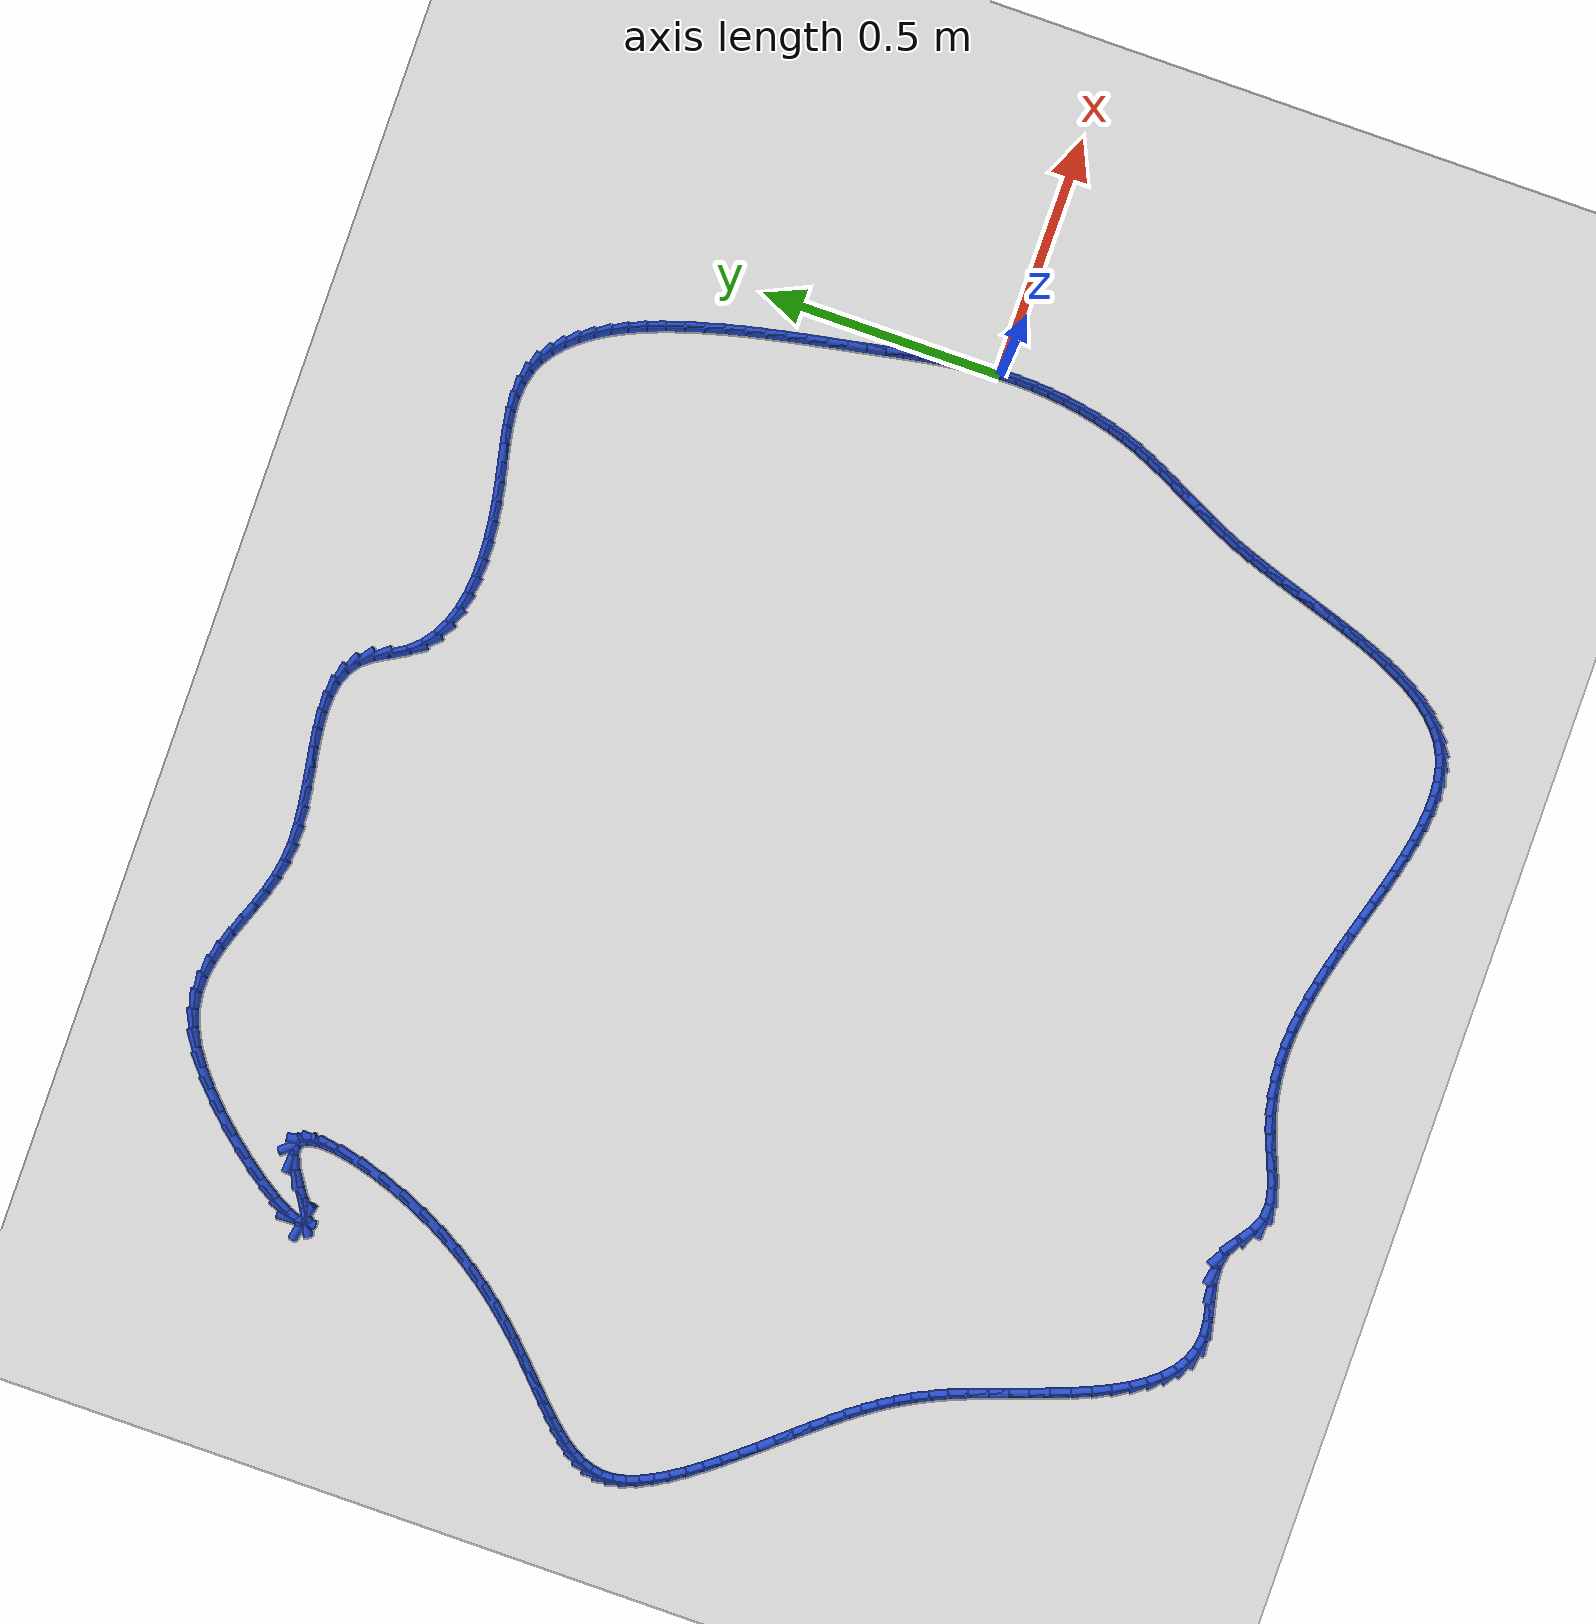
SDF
<sdf version="1.6">
 <world name="default">
  <light name="sun" type="directional">
   <pose>0 0 10 0 -0 0</pose>
   <diffuse>0.8 0.8 0.8 1</diffuse>
   <specular>0.2 0.2 0.2 1</specular>
   <attenuation>
    <range>1000</range>
    <constant>0.9</constant>
    <linear>0.01</linear>
    <quadratic>0.001</quadratic>
   </attenuation>
   <direction>-0.5 0.1 -0.9</direction>
  </light>
  <model name="ground_plane">
   <static>1</static>
   <link name="link">
    <collision name="collision">
     <geometry><plane><normal>0 0 1</normal><size>100 100</size></plane></geometry>
     <surface><friction><ode><mu>100</mu><mu2>50</mu2></ode></friction></surface>
    </collision>
    <visual name="visual">
     <cast_shadows>0</cast_shadows>
     <geometry><plane><normal>0 0 1</normal><size>100 100</size></plane></geometry>
     <material>
      <script><uri>file://media/materials/scripts/gazebo.material</uri><name>Gazebo/WhiteGlow</name></script>
     </material>
    </visual>
   </link>
  </model>
  <gravity>0 0 -9.8</gravity>
  <magnetic_field>6e-06 2.3e-05 -4.2e-05</magnetic_field>
  <atmosphere type="adiabatic"/>
  <physics name="default_physics" default="0" type="ode">
   <max_step_size>0.001</max_step_size>
   <real_time_factor>1</real_time_factor>
   <real_time_update_rate>1000</real_time_update_rate>
  </physics>
  <scene><ambient>0.4 0.4 0.4 1</ambient><background>0.7 0.7 0.7 1</background><shadows>1</shadows></scene>
  <spherical_coordinates>
   <surface_model>EARTH_WGS84</surface_model>
   <latitude_deg>0</latitude_deg>
   <longitude_deg>0</longitude_deg>
   <elevation>0</elevation>
   <heading_deg>0</heading_deg>
  </spherical_coordinates>
  <model name="line">
   <link name="link_0">
    <pose>8.673617379884035e-19 1.1102230246251565e-16 0.01 0 1.57 -1.5212087982481513</pose>
    <collision name="collision">
     <geometry><cylinder><radius>0.01</radius><length>0.08</length></cylinder></geometry>
    </collision>
    <visual name="visual">
     <material>
      <script><name>Gazebo/Blue</name><uri>file://media/materials/scripts/gazebo.material</uri></script>
     </material>
     <geometry><cylinder><radius>0.01</radius><length>0.08</length></cylinder></geometry>
    </visual>
   </link>
   <link name="link_1">
    <pose>-0.001661368765570098 0.0334762966615342 0.01 0 1.57 -1.4846151093203546</pose>
    <collision name="collision">
     <geometry><cylinder><radius>0.01</radius><length>0.08</length></cylinder></geometry>
    </collision>
    <visual name="visual">
     <material>
      <script><name>Gazebo/Blue</name><uri>file://media/materials/scripts/gazebo.material</uri></script>
     </material>
     <geometry><cylinder><radius>0.01</radius><length>0.08</length></cylinder></geometry>
    </visual>
   </link>
   <link name="link_2">
    <pose>-0.004521796959074508 0.06658493806401557 0.01 0 1.57 -1.4528000755124728</pose>
    <collision name="collision">
     <geometry><cylinder><radius>0.01</radius><length>0.08</length></cylinder></geometry>
    </collision>
    <visual name="visual">
     <material>
      <script><name>Gazebo/Blue</name><uri>file://media/materials/scripts/gazebo.material</uri></script>
     </material>
     <geometry><cylinder><radius>0.01</radius><length>0.08</length></cylinder></geometry>
    </visual>
   </link>
   <link name="link_3">
    <pose>-0.008432542661013587 0.09957394296238382 0.01 0 1.57 -1.4264953035481684</pose>
    <collision name="collision">
     <geometry><cylinder><radius>0.01</radius><length>0.08</length></cylinder></geometry>
    </collision>
    <visual name="visual">
     <material>
      <script><name>Gazebo/Blue</name><uri>file://media/materials/scripts/gazebo.material</uri></script>
     </material>
     <geometry><cylinder><radius>0.01</radius><length>0.08</length></cylinder></geometry>
    </visual>
   </link>
   <link name="link_4">
    <pose>-0.013244863951887703 0.13269133011157877 0.01 0 1.57 -1.4061456856873413</pose>
    <collision name="collision">
     <geometry><cylinder><radius>0.01</radius><length>0.08</length></cylinder></geometry>
    </collision>
    <visual name="visual">
     <material>
      <script><name>Gazebo/Blue</name><uri>file://media/materials/scripts/gazebo.material</uri></script>
     </material>
     <geometry><cylinder><radius>0.01</radius><length>0.08</length></cylinder></geometry>
    </visual>
   </link>
   <link name="link_5">
    <pose>-0.018810018912197222 0.16618511826654012 0.01 0 1.57 -1.391909453461869</pose>
    <collision name="collision">
     <geometry><cylinder><radius>0.01</radius><length>0.08</length></cylinder></geometry>
    </collision>
    <visual name="visual">
     <material>
      <script><name>Gazebo/Blue</name><uri>file://media/materials/scripts/gazebo.material</uri></script>
     </material>
     <geometry><cylinder><radius>0.01</radius><length>0.08</length></cylinder></geometry>
    </visual>
   </link>
   <link name="link_6">
    <pose>-0.024979265622442494 0.20030332618220742 0.01 0 1.57 -1.3836861519026695</pose>
    <collision name="collision">
     <geometry><cylinder><radius>0.01</radius><length>0.08</length></cylinder></geometry>
    </collision>
    <visual name="visual">
     <material>
      <script><name>Gazebo/Blue</name><uri>file://media/materials/scripts/gazebo.material</uri></script>
     </material>
     <geometry><cylinder><radius>0.01</radius><length>0.08</length></cylinder></geometry>
    </visual>
   </link>
   <link name="link_7">
    <pose>-0.0316038621631239 0.23529397261352053 0.01 0 1.57 -1.3811615950575682</pose>
    <collision name="collision">
     <geometry><cylinder><radius>0.01</radius><length>0.08</length></cylinder></geometry>
    </collision>
    <visual name="visual">
     <material>
      <script><name>Gazebo/Blue</name><uri>file://media/materials/scripts/gazebo.material</uri></script>
     </material>
     <geometry><cylinder><radius>0.01</radius><length>0.08</length></cylinder></geometry>
    </visual>
   </link>
   <link name="link_8">
    <pose>-0.0385350666147418 0.27140507631541905 0.01 0 1.57 -1.3832920208682706</pose>
    <collision name="collision">
     <geometry><cylinder><radius>0.01</radius><length>0.08</length></cylinder></geometry>
    </collision>
    <visual name="visual">
     <material>
      <script><name>Gazebo/Blue</name><uri>file://media/materials/scripts/gazebo.material</uri></script>
     </material>
     <geometry><cylinder><radius>0.01</radius><length>0.08</length></cylinder></geometry>
    </visual>
   </link>
   <link name="link_9">
    <pose>-0.045639557668936015 0.30884973998140686 0.01 0 1.57 -1.384328095523199</pose>
    <collision name="collision">
     <geometry><cylinder><radius>0.01</radius><length>0.08</length></cylinder></geometry>
    </collision>
    <visual name="visual">
     <material>
      <script><name>Gazebo/Blue</name><uri>file://media/materials/scripts/gazebo.material</uri></script>
     </material>
     <geometry><cylinder><radius>0.01</radius><length>0.08</length></cylinder></geometry>
    </visual>
   </link>
   <link name="link_10">
    <pose>-0.0529323098806072 0.3475052879479914 0.01 0 1.57 -1.381496522466564</pose>
    <collision name="collision">
     <geometry><cylinder><radius>0.01</radius><length>0.08</length></cylinder></geometry>
    </collision>
    <visual name="visual">
     <material>
      <script><name>Gazebo/Blue</name><uri>file://media/materials/scripts/gazebo.material</uri></script>
     </material>
     <geometry><cylinder><radius>0.01</radius><length>0.08</length></cylinder></geometry>
    </visual>
   </link>
   <link name="link_11">
    <pose>-0.0605110637291185 0.38706164211495525 0.01 0 1.57 -1.3749727827922171</pose>
    <collision name="collision">
     <geometry><cylinder><radius>0.01</radius><length>0.08</length></cylinder></geometry>
    </collision>
    <visual name="visual">
     <material>
      <script><name>Gazebo/Blue</name><uri>file://media/materials/scripts/gazebo.material</uri></script>
     </material>
     <geometry><cylinder><radius>0.01</radius><length>0.08</length></cylinder></geometry>
    </visual>
   </link>
   <link name="link_12">
    <pose>-0.06847446004382249 0.42720668576796444 0.01 0 1.57 -1.3647961792488679</pose>
    <collision name="collision">
     <geometry><cylinder><radius>0.01</radius><length>0.08</length></cylinder></geometry>
    </collision>
    <visual name="visual">
     <material>
      <script><name>Gazebo/Blue</name><uri>file://media/materials/scripts/gazebo.material</uri></script>
     </material>
     <geometry><cylinder><radius>0.01</radius><length>0.08</length></cylinder></geometry>
    </visual>
   </link>
   <link name="link_13">
    <pose>-0.07692113965407184 0.467628302192686 0.01 0 1.57 -1.3508554336957348</pose>
    <collision name="collision">
     <geometry><cylinder><radius>0.01</radius><length>0.08</length></cylinder></geometry>
    </collision>
    <visual name="visual">
     <material>
      <script><name>Gazebo/Blue</name><uri>file://media/materials/scripts/gazebo.material</uri></script>
     </material>
     <geometry><cylinder><radius>0.01</radius><length>0.08</length></cylinder></geometry>
    </visual>
   </link>
   <link name="link_14">
    <pose>-0.08594974338921907 0.5080143746747858 0.01 0 1.57 -1.3328922962845482</pose>
    <collision name="collision">
     <geometry><cylinder><radius>0.01</radius><length>0.08</length></cylinder></geometry>
    </collision>
    <visual name="visual">
     <material>
      <script><name>Gazebo/Blue</name><uri>file://media/materials/scripts/gazebo.material</uri></script>
     </material>
     <geometry><cylinder><radius>0.01</radius><length>0.08</length></cylinder></geometry>
    </visual>
   </link>
   <link name="link_15">
    <pose>-0.09565891207861685 0.5480527864999307 0.01 0 1.57 -1.3104925611236626</pose>
    <collision name="collision">
     <geometry><cylinder><radius>0.01</radius><length>0.08</length></cylinder></geometry>
    </collision>
    <visual name="visual">
     <material>
      <script><name>Gazebo/Blue</name><uri>file://media/materials/scripts/gazebo.material</uri></script>
     </material>
     <geometry><cylinder><radius>0.01</radius><length>0.08</length></cylinder></geometry>
    </visual>
   </link>
   <link name="link_16">
    <pose>-0.10614728655161779 0.5874314209537871 0.01 0 1.57 -1.2830653320867553</pose>
    <collision name="collision">
     <geometry><cylinder><radius>0.01</radius><length>0.08</length></cylinder></geometry>
    </collision>
    <visual name="visual">
     <material>
      <script><name>Gazebo/Blue</name><uri>file://media/materials/scripts/gazebo.material</uri></script>
     </material>
     <geometry><cylinder><radius>0.01</radius><length>0.08</length></cylinder></geometry>
    </visual>
   </link>
   <link name="link_17">
    <pose>-0.11751350763757448 0.6258381613220215 0.01 0 1.57 -1.2498104905205722</pose>
    <collision name="collision">
     <geometry><cylinder><radius>0.01</radius><length>0.08</length></cylinder></geometry>
    </collision>
    <visual name="visual">
     <material>
      <script><name>Gazebo/Blue</name><uri>file://media/materials/scripts/gazebo.material</uri></script>
     </material>
     <geometry><cylinder><radius>0.01</radius><length>0.08</length></cylinder></geometry>
    </visual>
   </link>
   <link name="link_18">
    <pose>-0.12985621616583953 0.6629608908903003 0.01 0 1.57 -1.2096744515808182</pose>
    <collision name="collision">
     <geometry><cylinder><radius>0.01</radius><length>0.08</length></cylinder></geometry>
    </collision>
    <visual name="visual">
     <material>
      <script><name>Gazebo/Blue</name><uri>file://media/materials/scripts/gazebo.material</uri></script>
     </material>
     <geometry><cylinder><radius>0.01</radius><length>0.08</length></cylinder></geometry>
    </visual>
   </link>
   <link name="link_19">
    <pose>-0.14327405296576548 0.6984874929442898 0.01 0 1.57 -1.1612963591561665</pose>
    <collision name="collision">
     <geometry><cylinder><radius>0.01</radius><length>0.08</length></cylinder></geometry>
    </collision>
    <visual name="visual">
     <material>
      <script><name>Gazebo/Blue</name><uri>file://media/materials/scripts/gazebo.material</uri></script>
     </material>
     <geometry><cylinder><radius>0.01</radius><length>0.08</length></cylinder></geometry>
    </visual>
   </link>
   <link name="link_20">
    <pose>-0.15786565886670506 0.7321058507696567 0.01 0 1.57 -1.1029530299818024</pose>
    <collision name="collision">
     <geometry><cylinder><radius>0.01</radius><length>0.08</length></cylinder></geometry>
    </collision>
    <visual name="visual">
     <material>
      <script><name>Gazebo/Blue</name><uri>file://media/materials/scripts/gazebo.material</uri></script>
     </material>
     <geometry><cylinder><radius>0.01</radius><length>0.08</length></cylinder></geometry>
    </visual>
   </link>
   <link name="link_21">
    <pose>-0.17372967469801076 0.7635038476520672 0.01 0 1.57 -1.0325255693916997</pose>
    <collision name="collision">
     <geometry><cylinder><radius>0.01</radius><length>0.08</length></cylinder></geometry>
    </collision>
    <visual name="visual">
     <material>
      <script><name>Gazebo/Blue</name><uri>file://media/materials/scripts/gazebo.material</uri></script>
     </material>
     <geometry><cylinder><radius>0.01</radius><length>0.08</length></cylinder></geometry>
    </visual>
   </link>
   <link name="link_22">
    <pose>-0.19096474128903523 0.792369366877188 0.01 0 1.57 -0.9475407839293734</pose>
    <collision name="collision">
     <geometry><cylinder><radius>0.01</radius><length>0.08</length></cylinder></geometry>
    </collision>
    <visual name="visual">
     <material>
      <script><name>Gazebo/Blue</name><uri>file://media/materials/scripts/gazebo.material</uri></script>
     </material>
     <geometry><cylinder><radius>0.01</radius><length>0.08</length></cylinder></geometry>
    </visual>
   </link>
   <link name="link_23">
    <pose>-0.20966949946913122 0.8183902917306858 0.01 0 1.57 -0.8453929556715997</pose>
    <collision name="collision">
     <geometry><cylinder><radius>0.01</radius><length>0.08</length></cylinder></geometry>
    </collision>
    <visual name="visual">
     <material>
      <script><name>Gazebo/Blue</name><uri>file://media/materials/scripts/gazebo.material</uri></script>
     </material>
     <geometry><cylinder><radius>0.01</radius><length>0.08</length></cylinder></geometry>
    </visual>
   </link>
   <link name="link_24">
    <pose>-0.2299425900676511 0.8412545054982264 0.01 0 1.57 -0.7239141213903106</pose>
    <collision name="collision">
     <geometry><cylinder><radius>0.01</radius><length>0.08</length></cylinder></geometry>
    </collision>
    <visual name="visual">
     <material>
      <script><name>Gazebo/Blue</name><uri>file://media/materials/scripts/gazebo.material</uri></script>
     </material>
     <geometry><cylinder><radius>0.01</radius><length>0.08</length></cylinder></geometry>
    </visual>
   </link>
   <link name="link_25">
    <pose>-0.25188265391394765 0.8606498914654769 0.01 0 1.57 -0.5824525466910896</pose>
    <collision name="collision">
     <geometry><cylinder><radius>0.01</radius><length>0.08</length></cylinder></geometry>
    </collision>
    <visual name="visual">
     <material>
      <script><name>Gazebo/Blue</name><uri>file://media/materials/scripts/gazebo.material</uri></script>
     </material>
     <geometry><cylinder><radius>0.01</radius><length>0.08</length></cylinder></geometry>
    </visual>
   </link>
   <link name="link_26">
    <pose>-0.27558833183737336 0.8762643329181032 0.01 0 1.57 -0.4233387469850311</pose>
    <collision name="collision">
     <geometry><cylinder><radius>0.01</radius><length>0.08</length></cylinder></geometry>
    </collision>
    <visual name="visual">
     <material>
      <script><name>Gazebo/Blue</name><uri>file://media/materials/scripts/gazebo.material</uri></script>
     </material>
     <geometry><cylinder><radius>0.01</radius><length>0.08</length></cylinder></geometry>
    </visual>
   </link>
   <link name="link_27">
    <pose>-0.30115826466728085 0.8877857131417721 0.01 0 1.57 -0.25292742398793955</pose>
    <collision name="collision">
     <geometry><cylinder><radius>0.01</radius><length>0.08</length></cylinder></geometry>
    </collision>
    <visual name="visual">
     <material>
      <script><name>Gazebo/Blue</name><uri>file://media/materials/scripts/gazebo.material</uri></script>
     </material>
     <geometry><cylinder><radius>0.01</radius><length>0.08</length></cylinder></geometry>
    </visual>
   </link>
   <link name="link_28">
    <pose>-0.3286910926172952 0.8949019181546274 0.01 0 1.57 -0.08816823567520314</pose>
    <collision name="collision">
     <geometry><cylinder><radius>0.01</radius><length>0.08</length></cylinder></geometry>
    </collision>
    <visual name="visual">
     <material>
      <script><name>Gazebo/Blue</name><uri>file://media/materials/scripts/gazebo.material</uri></script>
     </material>
     <geometry><cylinder><radius>0.01</radius><length>0.08</length></cylinder></geometry>
    </visual>
   </link>
   <link name="link_29">
    <pose>-0.3582374798571151 0.8975137422896868 0.01 0 1.57 0.03813340483004825</pose>
    <collision name="collision">
     <geometry><cylinder><radius>0.01</radius><length>0.08</length></cylinder></geometry>
    </collision>
    <visual name="visual">
     <material>
      <script><name>Gazebo/Blue</name><uri>file://media/materials/scripts/gazebo.material</uri></script>
     </material>
     <geometry><cylinder><radius>0.01</radius><length>0.08</length></cylinder></geometry>
    </visual>
   </link>
   <link name="link_30">
    <pose>-0.38966949520027166 0.8963145511970907 0.01 0 1.57 0.12402622890133069</pose>
    <collision name="collision">
     <geometry><cylinder><radius>0.01</radius><length>0.08</length></cylinder></geometry>
    </collision>
    <visual name="visual">
     <material>
      <script><name>Gazebo/Blue</name><uri>file://media/materials/scripts/gazebo.material</uri></script>
     </material>
     <geometry><cylinder><radius>0.01</radius><length>0.08</length></cylinder></geometry>
    </visual>
   </link>
   <link name="link_31">
    <pose>-0.422817658062107 0.892182098642972 0.01 0 1.57 0.17649809885115322</pose>
    <collision name="collision">
     <geometry><cylinder><radius>0.01</radius><length>0.08</length></cylinder></geometry>
    </collision>
    <visual name="visual">
     <material>
      <script><name>Gazebo/Blue</name><uri>file://media/materials/scripts/gazebo.material</uri></script>
     </material>
     <geometry><cylinder><radius>0.01</radius><length>0.08</length></cylinder></geometry>
    </visual>
   </link>
   <link name="link_32">
    <pose>-0.45751248785796317 0.8859941383934634 0.01 0 1.57 0.2014256434785553</pose>
    <collision name="collision">
     <geometry><cylinder><radius>0.01</radius><length>0.08</length></cylinder></geometry>
    </collision>
    <visual name="visual">
     <material>
      <script><name>Gazebo/Blue</name><uri>file://media/materials/scripts/gazebo.material</uri></script>
     </material>
     <geometry><cylinder><radius>0.01</radius><length>0.08</length></cylinder></geometry>
    </visual>
   </link>
   <link name="link_33">
    <pose>-0.49358450400318205 0.8786284242146976 0.01 0 1.57 0.20280015749197633</pose>
    <collision name="collision">
     <geometry><cylinder><radius>0.01</radius><length>0.08</length></cylinder></geometry>
    </collision>
    <visual name="visual">
     <material>
      <script><name>Gazebo/Blue</name><uri>file://media/materials/scripts/gazebo.material</uri></script>
     </material>
     <geometry><cylinder><radius>0.01</radius><length>0.08</length></cylinder></geometry>
    </visual>
   </link>
   <link name="link_34">
    <pose>-0.5308642259131058 0.8709627098728076 0.01 0 1.57 0.18300490091923768</pose>
    <collision name="collision">
     <geometry><cylinder><radius>0.01</radius><length>0.08</length></cylinder></geometry>
    </collision>
    <visual name="visual">
     <material>
      <script><name>Gazebo/Blue</name><uri>file://media/materials/scripts/gazebo.material</uri></script>
     </material>
     <geometry><cylinder><radius>0.01</radius><length>0.08</length></cylinder></geometry>
    </visual>
   </link>
   <link name="link_35">
    <pose>-0.5691796229734953 0.8638714632881843 0.01 0 1.57 0.1478902709736078</pose>
    <collision name="collision">
     <geometry><cylinder><radius>0.01</radius><length>0.08</length></cylinder></geometry>
    </collision>
    <visual name="visual">
     <material>
      <script><name>Gazebo/Blue</name><uri>file://media/materials/scripts/gazebo.material</uri></script>
     </material>
     <geometry><cylinder><radius>0.01</radius><length>0.08</length></cylinder></geometry>
    </visual>
   </link>
   <link name="link_36">
    <pose>-0.6082233604661803 0.8580548060061809 0.01 0 1.57 0.1040383420772358</pose>
    <collision name="collision">
     <geometry><cylinder><radius>0.01</radius><length>0.08</length></cylinder></geometry>
    </collision>
    <visual name="visual">
     <material>
      <script><name>Gazebo/Blue</name><uri>file://media/materials/scripts/gazebo.material</uri></script>
     </material>
     <geometry><cylinder><radius>0.01</radius><length>0.08</length></cylinder></geometry>
    </visual>
   </link>
   <link name="link_37">
    <pose>-0.647487970984176 0.8539549781937761 0.01 0 1.57 0.05030309757663659</pose>
    <collision name="collision">
     <geometry><cylinder><radius>0.01</radius><length>0.08</length></cylinder></geometry>
    </collision>
    <visual name="visual">
     <material>
      <script><name>Gazebo/Blue</name><uri>file://media/materials/scripts/gazebo.material</uri></script>
     </material>
     <geometry><cylinder><radius>0.01</radius><length>0.08</length></cylinder></geometry>
    </visual>
   </link>
   <link name="link_38">
    <pose>-0.6864498452975923 0.851993420439604 0.01 0 1.57 -0.01568363847617912</pose>
    <collision name="collision">
     <geometry><cylinder><radius>0.01</radius><length>0.08</length></cylinder></geometry>
    </collision>
    <visual name="visual">
     <material>
      <script><name>Gazebo/Blue</name><uri>file://media/materials/scripts/gazebo.material</uri></script>
     </material>
     <geometry><cylinder><radius>0.01</radius><length>0.08</length></cylinder></geometry>
    </visual>
   </link>
   <link name="link_39">
    <pose>-0.7245853741765391 0.8525915733322984 0.01 0 1.57 -0.0969965013836253</pose>
    <collision name="collision">
     <geometry><cylinder><radius>0.01</radius><length>0.08</length></cylinder></geometry>
    </collision>
    <visual name="visual">
     <material>
      <script><name>Gazebo/Blue</name><uri>file://media/materials/scripts/gazebo.material</uri></script>
     </material>
     <geometry><cylinder><radius>0.01</radius><length>0.08</length></cylinder></geometry>
    </visual>
   </link>
   <link name="link_40">
    <pose>-0.7613709483911258 0.8561708774604933 0.01 0 1.57 -0.1973816205993514</pose>
    <collision name="collision">
     <geometry><cylinder><radius>0.01</radius><length>0.08</length></cylinder></geometry>
    </collision>
    <visual name="visual">
     <material>
      <script><name>Gazebo/Blue</name><uri>file://media/materials/scripts/gazebo.material</uri></script>
     </material>
     <geometry><cylinder><radius>0.01</radius><length>0.08</length></cylinder></geometry>
    </visual>
   </link>
   <link name="link_41">
    <pose>-0.7962829587114624 0.8631527734128228 0.01 0 1.57 -0.3208548305307442</pose>
    <collision name="collision">
     <geometry><cylinder><radius>0.01</radius><length>0.08</length></cylinder></geometry>
    </collision>
    <visual name="visual">
     <material>
      <script><name>Gazebo/Blue</name><uri>file://media/materials/scripts/gazebo.material</uri></script>
     </material>
     <geometry><cylinder><radius>0.01</radius><length>0.08</length></cylinder></geometry>
    </visual>
   </link>
   <link name="link_42">
    <pose>-0.8287977959076587 0.8739587017779207 0.01 0 1.57 -0.47050029324037296</pose>
    <collision name="collision">
     <geometry><cylinder><radius>0.01</radius><length>0.08</length></cylinder></geometry>
    </collision>
    <visual name="visual">
     <material>
      <script><name>Gazebo/Blue</name><uri>file://media/materials/scripts/gazebo.material</uri></script>
     </material>
     <geometry><cylinder><radius>0.01</radius><length>0.08</length></cylinder></geometry>
    </visual>
   </link>
   <link name="link_43">
    <pose>-0.8583918507498245 0.8890101031444209 0.01 0 1.57 -0.6460920082147606</pose>
    <collision name="collision">
     <geometry><cylinder><radius>0.01</radius><length>0.08</length></cylinder></geometry>
    </collision>
    <visual name="visual">
     <material>
      <script><name>Gazebo/Blue</name><uri>file://media/materials/scripts/gazebo.material</uri></script>
     </material>
     <geometry><cylinder><radius>0.01</radius><length>0.08</length></cylinder></geometry>
    </visual>
   </link>
   <link name="link_44">
    <pose>-0.8845415140080692 0.9087284181009574 0.01 0 1.57 -0.841205230907671</pose>
    <collision name="collision">
     <geometry><cylinder><radius>0.01</radius><length>0.08</length></cylinder></geometry>
    </collision>
    <visual name="visual">
     <material>
      <script><name>Gazebo/Blue</name><uri>file://media/materials/scripts/gazebo.material</uri></script>
     </material>
     <geometry><cylinder><radius>0.01</radius><length>0.08</length></cylinder></geometry>
    </visual>
   </link>
   <link name="link_45">
    <pose>-0.9067231764525033 0.9335350872361645 0.01 0 1.57 -1.022542333226232</pose>
    <collision name="collision">
     <geometry><cylinder><radius>0.01</radius><length>0.08</length></cylinder></geometry>
    </collision>
    <visual name="visual">
     <material>
      <script><name>Gazebo/Blue</name><uri>file://media/materials/scripts/gazebo.material</uri></script>
     </material>
     <geometry><cylinder><radius>0.01</radius><length>0.08</length></cylinder></geometry>
    </visual>
   </link>
   <link name="link_46">
    <pose>-0.9248538283114025 0.9632231336911607 0.01 0 1.57 -1.0584157965612788</pose>
    <collision name="collision">
     <geometry><cylinder><radius>0.01</radius><length>0.08</length></cylinder></geometry>
    </collision>
    <visual name="visual">
     <material>
      <script><name>Gazebo/Blue</name><uri>file://media/materials/scripts/gazebo.material</uri></script>
     </material>
     <geometry><cylinder><radius>0.01</radius><length>0.08</length></cylinder></geometry>
    </visual>
   </link>
   <link name="link_47">
    <pose>-0.9418088713638217 0.9933660624007312 0.01 0 1.57 -0.8980096886420139</pose>
    <collision name="collision">
     <geometry><cylinder><radius>0.01</radius><length>0.08</length></cylinder></geometry>
    </collision>
    <visual name="visual">
     <material>
      <script><name>Gazebo/Blue</name><uri>file://media/materials/scripts/gazebo.material</uri></script>
     </material>
     <geometry><cylinder><radius>0.01</radius><length>0.08</length></cylinder></geometry>
    </visual>
   </link>
   <link name="link_48">
    <pose>-0.9615020848817856 1.018081442661707 0.01 0 1.57 -0.6288896149423155</pose>
    <collision name="collision">
     <geometry><cylinder><radius>0.01</radius><length>0.08</length></cylinder></geometry>
    </collision>
    <visual name="visual">
     <material>
      <script><name>Gazebo/Blue</name><uri>file://media/materials/scripts/gazebo.material</uri></script>
     </material>
     <geometry><cylinder><radius>0.01</radius><length>0.08</length></cylinder></geometry>
    </visual>
   </link>
   <link name="link_49">
    <pose>-0.985336703452387 1.0354191119622747 0.01 0 1.57 -0.3773623143663472</pose>
    <collision name="collision">
     <geometry><cylinder><radius>0.01</radius><length>0.08</length></cylinder></geometry>
    </collision>
    <visual name="visual">
     <material>
      <script><name>Gazebo/Blue</name><uri>file://media/materials/scripts/gazebo.material</uri></script>
     </material>
     <geometry><cylinder><radius>0.01</radius><length>0.08</length></cylinder></geometry>
    </visual>
   </link>
   <link name="link_50">
    <pose>-1.0128637384003396 1.0463296575100602 0.01 0 1.57 -0.1771639495743758</pose>
    <collision name="collision">
     <geometry><cylinder><radius>0.01</radius><length>0.08</length></cylinder></geometry>
    </collision>
    <visual name="visual">
     <material>
      <script><name>Gazebo/Blue</name><uri>file://media/materials/scripts/gazebo.material</uri></script>
     </material>
     <geometry><cylinder><radius>0.01</radius><length>0.08</length></cylinder></geometry>
    </visual>
   </link>
   <link name="link_51">
    <pose>-1.0435911283031478 1.0518311223436991 0.01 0 1.57 -0.03319863875413387</pose>
    <collision name="collision">
     <geometry><cylinder><radius>0.01</radius><length>0.08</length></cylinder></geometry>
    </collision>
    <visual name="visual">
     <material>
      <script><name>Gazebo/Blue</name><uri>file://media/materials/scripts/gazebo.material</uri></script>
     </material>
     <geometry><cylinder><radius>0.01</radius><length>0.08</length></cylinder></geometry>
    </visual>
   </link>
   <link name="link_52">
    <pose>-1.0770268117383157 1.0529415495018273 0.01 0 1.57 0.06337772470116944</pose>
    <collision name="collision">
     <geometry><cylinder><radius>0.01</radius><length>0.08</length></cylinder></geometry>
    </collision>
    <visual name="visual">
     <material>
      <script><name>Gazebo/Blue</name><uri>file://media/materials/scripts/gazebo.material</uri></script>
     </material>
     <geometry><cylinder><radius>0.01</radius><length>0.08</length></cylinder></geometry>
    </visual>
   </link>
   <link name="link_53">
    <pose>-1.1126787272833478 1.0506789820230809 0.01 0 1.57 0.1229192380008859</pose>
    <collision name="collision">
     <geometry><cylinder><radius>0.01</radius><length>0.08</length></cylinder></geometry>
    </collision>
    <visual name="visual">
     <material>
      <script><name>Gazebo/Blue</name><uri>file://media/materials/scripts/gazebo.material</uri></script>
     </material>
     <geometry><cylinder><radius>0.01</radius><length>0.08</length></cylinder></geometry>
    </visual>
   </link>
   <link name="link_54">
    <pose>-1.1500548135157482 1.0460614629460963 0.01 0 1.57 0.1530213847281046</pose>
    <collision name="collision">
     <geometry><cylinder><radius>0.01</radius><length>0.08</length></cylinder></geometry>
    </collision>
    <visual name="visual">
     <material>
      <script><name>Gazebo/Blue</name><uri>file://media/materials/scripts/gazebo.material</uri></script>
     </material>
     <geometry><cylinder><radius>0.01</radius><length>0.08</length></cylinder></geometry>
    </visual>
   </link>
   <link name="link_55">
    <pose>-1.1886630090130217 1.040107035309509 0.01 0 1.57 0.15809950804738554</pose>
    <collision name="collision">
     <geometry><cylinder><radius>0.01</radius><length>0.08</length></cylinder></geometry>
    </collision>
    <visual name="visual">
     <material>
      <script><name>Gazebo/Blue</name><uri>file://media/materials/scripts/gazebo.material</uri></script>
     </material>
     <geometry><cylinder><radius>0.01</radius><length>0.08</length></cylinder></geometry>
    </visual>
   </link>
   <link name="link_56">
    <pose>-1.228011252352672 1.0338337421519548 0.01 0 1.57 0.13985488262994417</pose>
    <collision name="collision">
     <geometry><cylinder><radius>0.01</radius><length>0.08</length></cylinder></geometry>
    </collision>
    <visual name="visual">
     <material>
      <script><name>Gazebo/Blue</name><uri>file://media/materials/scripts/gazebo.material</uri></script>
     </material>
     <geometry><cylinder><radius>0.01</radius><length>0.08</length></cylinder></geometry>
    </visual>
   </link>
   <link name="link_57">
    <pose>-1.267607482112205 1.0282596265120705 0.01 0 1.57 0.09769772799467649</pose>
    <collision name="collision">
     <geometry><cylinder><radius>0.01</radius><length>0.08</length></cylinder></geometry>
    </collision>
    <visual name="visual">
     <material>
      <script><name>Gazebo/Blue</name><uri>file://media/materials/scripts/gazebo.material</uri></script>
     </material>
     <geometry><cylinder><radius>0.01</radius><length>0.08</length></cylinder></geometry>
    </visual>
   </link>
   <link name="link_58">
    <pose>-1.3069596368691236 1.0244027314284916 0.01 0 1.57 0.029037593023130994</pose>
    <collision name="collision">
     <geometry><cylinder><radius>0.01</radius><length>0.08</length></cylinder></geometry>
    </collision>
    <visual name="visual">
     <material>
      <script><name>Gazebo/Blue</name><uri>file://media/materials/scripts/gazebo.material</uri></script>
     </material>
     <geometry><cylinder><radius>0.01</radius><length>0.08</length></cylinder></geometry>
    </visual>
   </link>
   <link name="link_59">
    <pose>-1.3455756552009326 1.0232810999398543 0.01 0 1.57 -0.06986609626047219</pose>
    <collision name="collision">
     <geometry><cylinder><radius>0.01</radius><length>0.08</length></cylinder></geometry>
    </collision>
    <visual name="visual">
     <material>
      <script><name>Gazebo/Blue</name><uri>file://media/materials/scripts/gazebo.material</uri></script>
     </material>
     <geometry><cylinder><radius>0.01</radius><length>0.08</length></cylinder></geometry>
    </visual>
   </link>
   <link name="link_60">
    <pose>-1.3829688667156486 1.0258978767738631 0.01 0 1.57 -0.18056665489747512</pose>
    <collision name="collision">
     <geometry><cylinder><radius>0.01</radius><length>0.08</length></cylinder></geometry>
    </collision>
    <visual name="visual">
     <material>
      <script><name>Gazebo/Blue</name><uri>file://media/materials/scripts/gazebo.material</uri></script>
     </material>
     <geometry><cylinder><radius>0.01</radius><length>0.08</length></cylinder></geometry>
    </visual>
   </link>
   <link name="link_61">
    <pose>-1.4189391112707923 1.0324644250550838 0.01 0 1.57 -0.2681983080207443</pose>
    <collision name="collision">
     <geometry><cylinder><radius>0.01</radius><length>0.08</length></cylinder></geometry>
    </collision>
    <visual name="visual">
     <material>
      <script><name>Gazebo/Blue</name><uri>file://media/materials/scripts/gazebo.material</uri></script>
     </material>
     <geometry><cylinder><radius>0.01</radius><length>0.08</length></cylinder></geometry>
    </visual>
   </link>
   <link name="link_62">
    <pose>-1.4537102831497049 1.042020217919219 0.01 0 1.57 -0.32741073580321023</pose>
    <collision name="collision">
     <geometry><cylinder><radius>0.01</radius><length>0.08</length></cylinder></geometry>
    </collision>
    <visual name="visual">
     <material>
      <script><name>Gazebo/Blue</name><uri>file://media/materials/scripts/gazebo.material</uri></script>
     </material>
     <geometry><cylinder><radius>0.01</radius><length>0.08</length></cylinder></geometry>
    </visual>
   </link>
   <link name="link_63">
    <pose>-1.4875405091364668 1.0535101257282136 0.01 0 1.57 -0.3571461313098198</pose>
    <collision name="collision">
     <geometry><cylinder><radius>0.01</radius><length>0.08</length></cylinder></geometry>
    </collision>
    <visual name="visual">
     <material>
      <script><name>Gazebo/Blue</name><uri>file://media/materials/scripts/gazebo.material</uri></script>
     </material>
     <geometry><cylinder><radius>0.01</radius><length>0.08</length></cylinder></geometry>
    </visual>
   </link>
   <link name="link_64">
    <pose>-1.5206879160151592 1.0658790188440124 0.01 0 1.57 -0.3566720225076159</pose>
    <collision name="collision">
     <geometry><cylinder><radius>0.01</radius><length>0.08</length></cylinder></geometry>
    </collision>
    <visual name="visual">
     <material>
      <script><name>Gazebo/Blue</name><uri>file://media/materials/scripts/gazebo.material</uri></script>
     </material>
     <geometry><cylinder><radius>0.01</radius><length>0.08</length></cylinder></geometry>
    </visual>
   </link>
   <link name="link_65">
    <pose>-1.55341063056986 1.0780717676285592 0.01 0 1.57 -0.3247725065992982</pose>
    <collision name="collision">
     <geometry><cylinder><radius>0.01</radius><length>0.08</length></cylinder></geometry>
    </collision>
    <visual name="visual">
     <material>
      <script><name>Gazebo/Blue</name><uri>file://media/materials/scripts/gazebo.material</uri></script>
     </material>
     <geometry><cylinder><radius>0.01</radius><length>0.08</length></cylinder></geometry>
    </visual>
   </link>
   <link name="link_66">
    <pose>-1.5859667795846524 1.0890332424438 0.01 0 1.57 -0.2597161242606549</pose>
    <collision name="collision">
     <geometry><cylinder><radius>0.01</radius><length>0.08</length></cylinder></geometry>
    </collision>
    <visual name="visual">
     <material>
      <script><name>Gazebo/Blue</name><uri>file://media/materials/scripts/gazebo.material</uri></script>
     </material>
     <geometry><cylinder><radius>0.01</radius><length>0.08</length></cylinder></geometry>
    </visual>
   </link>
   <link name="link_67">
    <pose>-1.618614489843614 1.0977083136516783 0.01 0 1.57 -0.16024914616022157</pose>
    <collision name="collision">
     <geometry><cylinder><radius>0.01</radius><length>0.08</length></cylinder></geometry>
    </collision>
    <visual name="visual">
     <material>
      <script><name>Gazebo/Blue</name><uri>file://media/materials/scripts/gazebo.material</uri></script>
     </material>
     <geometry><cylinder><radius>0.01</radius><length>0.08</length></cylinder></geometry>
    </visual>
   </link>
   <link name="link_68">
    <pose>-1.6516118881308255 1.1030418516141387 0.01 0 1.57 -0.02787164201527652</pose>
    <collision name="collision">
     <geometry><cylinder><radius>0.01</radius><length>0.08</length></cylinder></geometry>
    </collision>
    <visual name="visual">
     <material>
      <script><name>Gazebo/Blue</name><uri>file://media/materials/scripts/gazebo.material</uri></script>
     </material>
     <geometry><cylinder><radius>0.01</radius><length>0.08</length></cylinder></geometry>
    </visual>
   </link>
   <link name="link_69">
    <pose>-1.6852171012303667 1.103978726693126 0.01 0 1.57 0.1302353335444501</pose>
    <collision name="collision">
     <geometry><cylinder><radius>0.01</radius><length>0.08</length></cylinder></geometry>
    </collision>
    <visual name="visual">
     <material>
      <script><name>Gazebo/Blue</name><uri>file://media/materials/scripts/gazebo.material</uri></script>
     </material>
     <geometry><cylinder><radius>0.01</radius><length>0.08</length></cylinder></geometry>
    </visual>
   </link>
   <link name="link_70">
    <pose>-1.7196882559263191 1.099463809250585 0.01 0 1.57 0.3002806532966259</pose>
    <collision name="collision">
     <geometry><cylinder><radius>0.01</radius><length>0.08</length></cylinder></geometry>
    </collision>
    <visual name="visual">
     <material>
      <script><name>Gazebo/Blue</name><uri>file://media/materials/scripts/gazebo.material</uri></script>
     </material>
     <geometry><cylinder><radius>0.01</radius><length>0.08</length></cylinder></geometry>
    </visual>
   </link>
   <link name="link_71">
    <pose>-1.755283479002761 1.0884419696484602 0.01 0 1.57 0.46568175596118044</pose>
    <collision name="collision">
     <geometry><cylinder><radius>0.01</radius><length>0.08</length></cylinder></geometry>
    </collision>
    <visual name="visual">
     <material>
      <script><name>Gazebo/Blue</name><uri>file://media/materials/scripts/gazebo.material</uri></script>
     </material>
     <geometry><cylinder><radius>0.01</radius><length>0.08</length></cylinder></geometry>
    </visual>
   </link>
   <link name="link_72">
    <pose>-1.7922602406330903 1.0698594727714417 0.01 0 1.57 0.6049869766005426</pose>
    <collision name="collision">
     <geometry><cylinder><radius>0.01</radius><length>0.08</length></cylinder></geometry>
    </collision>
    <visual name="visual">
     <material>
      <script><name>Gazebo/Blue</name><uri>file://media/materials/scripts/gazebo.material</uri></script>
     </material>
     <geometry><cylinder><radius>0.01</radius><length>0.08</length></cylinder></geometry>
    </visual>
   </link>
   <link name="link_73">
    <pose>-1.8305306038181879 1.0433961660830882 0.01 0 1.57 0.7037240878594754</pose>
    <collision name="collision">
     <geometry><cylinder><radius>0.01</radius><length>0.08</length></cylinder></geometry>
    </collision>
    <visual name="visual">
     <material>
      <script><name>Gazebo/Blue</name><uri>file://media/materials/scripts/gazebo.material</uri></script>
     </material>
     <geometry><cylinder><radius>0.01</radius><length>0.08</length></cylinder></geometry>
    </visual>
   </link>
   <link name="link_74">
    <pose>-1.8690953881344594 1.0106672138397081 0.01 0 1.57 0.7767391319532617</pose>
    <collision name="collision">
     <geometry><cylinder><radius>0.01</radius><length>0.08</length></cylinder></geometry>
    </collision>
    <visual name="visual">
     <material>
      <script><name>Gazebo/Blue</name><uri>file://media/materials/scripts/gazebo.material</uri></script>
     </material>
     <geometry><cylinder><radius>0.01</radius><length>0.08</length></cylinder></geometry>
    </visual>
   </link>
   <link name="link_75">
    <pose>-1.906806894485441 0.9736032071900574 0.01 0 1.57 0.8353431667425341</pose>
    <collision name="collision">
     <geometry><cylinder><radius>0.01</radius><length>0.08</length></cylinder></geometry>
    </collision>
    <visual name="visual">
     <material>
      <script><name>Gazebo/Blue</name><uri>file://media/materials/scripts/gazebo.material</uri></script>
     </material>
     <geometry><cylinder><radius>0.01</radius><length>0.08</length></cylinder></geometry>
    </visual>
   </link>
   <link name="link_76">
    <pose>-1.9425174237746672 0.9341347372828884 0.01 0 1.57 0.8868426931191782</pose>
    <collision name="collision">
     <geometry><cylinder><radius>0.01</radius><length>0.08</length></cylinder></geometry>
    </collision>
    <visual name="visual">
     <material>
      <script><name>Gazebo/Blue</name><uri>file://media/materials/scripts/gazebo.material</uri></script>
     </material>
     <geometry><cylinder><radius>0.01</radius><length>0.08</length></cylinder></geometry>
    </visual>
   </link>
   <link name="link_77">
    <pose>-1.9750792769056722 0.8941923952669565 0.01 0 1.57 0.937326582108618</pose>
    <collision name="collision">
     <geometry><cylinder><radius>0.01</radius><length>0.08</length></cylinder></geometry>
    </collision>
    <visual name="visual">
     <material>
      <script><name>Gazebo/Blue</name><uri>file://media/materials/scripts/gazebo.material</uri></script>
     </material>
     <geometry><cylinder><radius>0.01</radius><length>0.08</length></cylinder></geometry>
    </visual>
   </link>
   <link name="link_78">
    <pose>-2.0033447547819927 0.8557067722910146 0.01 0 1.57 0.9942708983284558</pose>
    <collision name="collision">
     <geometry><cylinder><radius>0.01</radius><length>0.08</length></cylinder></geometry>
    </collision>
    <visual name="visual">
     <material>
      <script><name>Gazebo/Blue</name><uri>file://media/materials/scripts/gazebo.material</uri></script>
     </material>
     <geometry><cylinder><radius>0.01</radius><length>0.08</length></cylinder></geometry>
    </visual>
   </link>
   <link name="link_79">
    <pose>-2.026166158307163 0.8206084595038179 0.01 0 1.57 1.0718179621093586</pose>
    <collision name="collision">
     <geometry><cylinder><radius>0.01</radius><length>0.08</length></cylinder></geometry>
    </collision>
    <visual name="visual">
     <material>
      <script><name>Gazebo/Blue</name><uri>file://media/materials/scripts/gazebo.material</uri></script>
     </material>
     <geometry><cylinder><radius>0.01</radius><length>0.08</length></cylinder></geometry>
    </visual>
   </link>
   <link name="link_80">
    <pose>-2.042395788384718 0.7908280480541194 0.01 0 1.57 1.2104434385070313</pose>
    <collision name="collision">
     <geometry><cylinder><radius>0.01</radius><length>0.08</length></cylinder></geometry>
    </collision>
    <visual name="visual">
     <material>
      <script><name>Gazebo/Blue</name><uri>file://media/materials/scripts/gazebo.material</uri></script>
     </material>
     <geometry><cylinder><radius>0.01</radius><length>0.08</length></cylinder></geometry>
    </visual>
   </link>
   <link name="link_81">
    <pose>-2.050885945918193 0.768296129090674 0.01 0 1.57 -1.5410725139045</pose>
    <collision name="collision">
     <geometry><cylinder><radius>0.01</radius><length>0.08</length></cylinder></geometry>
    </collision>
    <visual name="visual">
     <material>
      <script><name>Gazebo/Blue</name><uri>file://media/materials/scripts/gazebo.material</uri></script>
     </material>
     <geometry><cylinder><radius>0.01</radius><length>0.08</length></cylinder></geometry>
    </visual>
   </link>
   <link name="link_82">
    <pose>-2.050488931811124 0.7549432937622355 0.01 0 1.57 -0.2118041331373783</pose>
    <collision name="collision">
     <geometry><cylinder><radius>0.01</radius><length>0.08</length></cylinder></geometry>
    </collision>
    <visual name="visual">
     <material>
      <script><name>Gazebo/Blue</name><uri>file://media/materials/scripts/gazebo.material</uri></script>
     </material>
     <geometry><cylinder><radius>0.01</radius><length>0.08</length></cylinder></geometry>
    </visual>
   </link>
   <link name="link_83">
    <pose>-2.0400570469670445 0.7527001332175576 0.01 0 1.57 0.45744897487119424</pose>
    <collision name="collision">
     <geometry><cylinder><radius>0.01</radius><length>0.08</length></cylinder></geometry>
    </collision>
    <visual name="visual">
     <material>
      <script><name>Gazebo/Blue</name><uri>file://media/materials/scripts/gazebo.material</uri></script>
     </material>
     <geometry><cylinder><radius>0.01</radius><length>0.08</length></cylinder></geometry>
    </visual>
   </link>
   <link name="link_84">
    <pose>-2.0186049973808413 0.7632604527032448 0.01 0 1.57 0.5866027108496537</pose>
    <collision name="collision">
     <geometry><cylinder><radius>0.01</radius><length>0.08</length></cylinder></geometry>
    </collision>
    <visual name="visual">
     <material>
      <script><name>Gazebo/Blue</name><uri>file://media/materials/scripts/gazebo.material</uri></script>
     </material>
     <geometry><cylinder><radius>0.01</radius><length>0.08</length></cylinder></geometry>
    </visual>
   </link>
   <link name="link_85">
    <pose>-1.9887022792217361 0.7831351891740828 0.01 0 1.57 0.5686621309636046</pose>
    <collision name="collision">
     <geometry><cylinder><radius>0.01</radius><length>0.08</length></cylinder></geometry>
    </collision>
    <visual name="visual">
     <material>
      <script><name>Gazebo/Blue</name><uri>file://media/materials/scripts/gazebo.material</uri></script>
     </material>
     <geometry><cylinder><radius>0.01</radius><length>0.08</length></cylinder></geometry>
    </visual>
   </link>
   <link name="link_86">
    <pose>-1.9563756877687135 0.8037945528323589 0.01 0 1.57 0.418411751020627</pose>
    <collision name="collision">
     <geometry><cylinder><radius>0.01</radius><length>0.08</length></cylinder></geometry>
    </collision>
    <visual name="visual">
     <material>
      <script><name>Gazebo/Blue</name><uri>file://media/materials/scripts/gazebo.material</uri></script>
     </material>
     <geometry><cylinder><radius>0.01</radius><length>0.08</length></cylinder></geometry>
    </visual>
   </link>
   <link name="link_87">
    <pose>-1.9277920971813378 0.8165047867914021 0.01 0 1.57 -0.06653541990882483</pose>
    <collision name="collision">
     <geometry><cylinder><radius>0.01</radius><length>0.08</length></cylinder></geometry>
    </collision>
    <visual name="visual">
     <material>
      <script><name>Gazebo/Blue</name><uri>file://media/materials/scripts/gazebo.material</uri></script>
     </material>
     <geometry><cylinder><radius>0.01</radius><length>0.08</length></cylinder></geometry>
    </visual>
   </link>
   <link name="link_88">
    <pose>-1.9074334913399102 0.8151482159827474 0.01 0 1.57 -0.8723620137242741</pose>
    <collision name="collision">
     <geometry><cylinder><radius>0.01</radius><length>0.08</length></cylinder></geometry>
    </collision>
    <visual name="visual">
     <material>
      <script><name>Gazebo/Blue</name><uri>file://media/materials/scripts/gazebo.material</uri></script>
     </material>
     <geometry><cylinder><radius>0.01</radius><length>0.08</length></cylinder></geometry>
    </visual>
   </link>
   <link name="link_89">
    <pose>-1.895252271215366 0.8006401215126245 0.01 0 1.57 -1.3850871233922117</pose>
    <collision name="collision">
     <geometry><cylinder><radius>0.01</radius><length>0.08</length></cylinder></geometry>
    </collision>
    <visual name="visual">
     <material>
      <script><name>Gazebo/Blue</name><uri>file://media/materials/scripts/gazebo.material</uri></script>
     </material>
     <geometry><cylinder><radius>0.01</radius><length>0.08</length></cylinder></geometry>
    </visual>
   </link>
   <link name="link_90">
    <pose>-1.8904474689103934 0.7750655191714086 0.01 0 1.57 1.5196012927165397</pose>
    <collision name="collision">
     <geometry><cylinder><radius>0.01</radius><length>0.08</length></cylinder></geometry>
    </collision>
    <visual name="visual">
     <material>
      <script><name>Gazebo/Blue</name><uri>file://media/materials/scripts/gazebo.material</uri></script>
     </material>
     <geometry><cylinder><radius>0.01</radius><length>0.08</length></cylinder></geometry>
    </visual>
   </link>
   <link name="link_91">
    <pose>-1.8922181165276777 0.740509424749473 0.01 0 1.57 1.3907490449269608</pose>
    <collision name="collision">
     <geometry><cylinder><radius>0.01</radius><length>0.08</length></cylinder></geometry>
    </collision>
    <visual name="visual">
     <material>
      <script><name>Gazebo/Blue</name><uri>file://media/materials/scripts/gazebo.material</uri></script>
     </material>
     <geometry><cylinder><radius>0.01</radius><length>0.08</length></cylinder></geometry>
    </visual>
   </link>
   <link name="link_92">
    <pose>-1.8997632461699057 0.6990568540371933 0.01 0 1.57 1.3065334629242669</pose>
    <collision name="collision">
     <geometry><cylinder><radius>0.01</radius><length>0.08</length></cylinder></geometry>
    </collision>
    <visual name="visual">
     <material>
      <script><name>Gazebo/Blue</name><uri>file://media/materials/scripts/gazebo.material</uri></script>
     </material>
     <geometry><cylinder><radius>0.01</radius><length>0.08</length></cylinder></geometry>
    </visual>
   </link>
   <link name="link_93">
    <pose>-1.9122818899397642 0.652792822824943 0.01 0 1.57 1.2424280225285025</pose>
    <collision name="collision">
     <geometry><cylinder><radius>0.01</radius><length>0.08</length></cylinder></geometry>
    </collision>
    <visual name="visual">
     <material>
      <script><name>Gazebo/Blue</name><uri>file://media/materials/scripts/gazebo.material</uri></script>
     </material>
     <geometry><cylinder><radius>0.01</radius><length>0.08</length></cylinder></geometry>
    </visual>
   </link>
   <link name="link_94">
    <pose>-1.9289730799399385 0.6038023469030974 0.01 0 1.57 1.1866476265695902</pose>
    <collision name="collision">
     <geometry><cylinder><radius>0.01</radius><length>0.08</length></cylinder></geometry>
    </collision>
    <visual name="visual">
     <material>
      <script><name>Gazebo/Blue</name><uri>file://media/materials/scripts/gazebo.material</uri></script>
     </material>
     <geometry><cylinder><radius>0.01</radius><length>0.08</length></cylinder></geometry>
    </visual>
   </link>
   <link name="link_95">
    <pose>-1.9490358482731165 0.5541704420620301 0.01 0 1.57 1.1316926501844684</pose>
    <collision name="collision">
     <geometry><cylinder><radius>0.01</radius><length>0.08</length></cylinder></geometry>
    </collision>
    <visual name="visual">
     <material>
      <script><name>Gazebo/Blue</name><uri>file://media/materials/scripts/gazebo.material</uri></script>
     </material>
     <geometry><cylinder><radius>0.01</radius><length>0.08</length></cylinder></geometry>
    </visual>
   </link>
   <link name="link_96">
    <pose>-1.9716692270419829 0.5059821240921165 0.01 0 1.57 1.0723572215384916</pose>
    <collision name="collision">
     <geometry><cylinder><radius>0.01</radius><length>0.08</length></cylinder></geometry>
    </collision>
    <visual name="visual">
     <material>
      <script><name>Gazebo/Blue</name><uri>file://media/materials/scripts/gazebo.material</uri></script>
     </material>
     <geometry><cylinder><radius>0.01</radius><length>0.08</length></cylinder></geometry>
    </visual>
   </link>
   <link name="link_97">
    <pose>-1.996122802162982 0.46105361581525356 0.01 0 1.57 1.0132516372227227</pose>
    <collision name="collision">
     <geometry><cylinder><radius>0.01</radius><length>0.08</length></cylinder></geometry>
    </collision>
    <visual name="visual">
     <material>
      <script><name>Gazebo/Blue</name><uri>file://media/materials/scripts/gazebo.material</uri></script>
     </material>
     <geometry><cylinder><radius>0.01</radius><length>0.08</length></cylinder></geometry>
    </visual>
   </link>
   <link name="link_98">
    <pose>-2.021937251558968 0.4196534134094386 0.01 0 1.57 0.9581274213804175</pose>
    <collision name="collision">
     <geometry><cylinder><radius>0.01</radius><length>0.08</length></cylinder></geometry>
    </collision>
    <visual name="visual">
     <material>
      <script><name>Gazebo/Blue</name><uri>file://media/materials/scripts/gazebo.material</uri></script>
     </material>
     <geometry><cylinder><radius>0.01</radius><length>0.08</length></cylinder></geometry>
    </visual>
   </link>
   <link name="link_99">
    <pose>-2.0487572288806786 0.38149717752018314 0.01 0 1.57 0.9080804795161215</pose>
    <collision name="collision">
     <geometry><cylinder><radius>0.01</radius><length>0.08</length></cylinder></geometry>
    </collision>
    <visual name="visual">
     <material>
      <script><name>Gazebo/Blue</name><uri>file://media/materials/scripts/gazebo.material</uri></script>
     </material>
     <geometry><cylinder><radius>0.01</radius><length>0.08</length></cylinder></geometry>
    </visual>
   </link>
   <link name="link_100">
    <pose>-2.0762275175373337 0.3462998788714076 0.01 0 1.57 0.864155209496878</pose>
    <collision name="collision">
     <geometry><cylinder><radius>0.01</radius><length>0.08</length></cylinder></geometry>
    </collision>
    <visual name="visual">
     <material>
      <script><name>Gazebo/Blue</name><uri>file://media/materials/scripts/gazebo.material</uri></script>
     </material>
     <geometry><cylinder><radius>0.01</radius><length>0.08</length></cylinder></geometry>
    </visual>
   </link>
   <link name="link_101">
    <pose>-2.1039929009381533 0.31377648818703463 0.01 0 1.57 0.8273731475131207</pose>
    <collision name="collision">
     <geometry><cylinder><radius>0.01</radius><length>0.08</length></cylinder></geometry>
    </collision>
    <visual name="visual">
     <material>
      <script><name>Gazebo/Blue</name><uri>file://media/materials/scripts/gazebo.material</uri></script>
     </material>
     <geometry><cylinder><radius>0.01</radius><length>0.08</length></cylinder></geometry>
    </visual>
   </link>
   <link name="link_102">
    <pose>-2.131698162492358 0.2836419761909852 0.01 0 1.57 0.798787305850978</pose>
    <collision name="collision">
     <geometry><cylinder><radius>0.01</radius><length>0.08</length></cylinder></geometry>
    </collision>
    <visual name="visual">
     <material>
      <script><name>Gazebo/Blue</name><uri>file://media/materials/scripts/gazebo.material</uri></script>
     </material>
     <geometry><cylinder><radius>0.01</radius><length>0.08</length></cylinder></geometry>
    </visual>
   </link>
   <link name="link_103">
    <pose>-2.1589880856091663 0.25561131360718153 0.01 0 1.57 0.7795662822124668</pose>
    <collision name="collision">
     <geometry><cylinder><radius>0.01</radius><length>0.08</length></cylinder></geometry>
    </collision>
    <visual name="visual">
     <material>
      <script><name>Gazebo/Blue</name><uri>file://media/materials/scripts/gazebo.material</uri></script>
     </material>
     <geometry><cylinder><radius>0.01</radius><length>0.08</length></cylinder></geometry>
    </visual>
   </link>
   <link name="link_104">
    <pose>-2.1855074536978005 0.22939947115954462 0.01 0 1.57 0.7711087160302562</pose>
    <collision name="collision">
     <geometry><cylinder><radius>0.01</radius><length>0.08</length></cylinder></geometry>
    </collision>
    <visual name="visual">
     <material>
      <script><name>Gazebo/Blue</name><uri>file://media/materials/scripts/gazebo.material</uri></script>
     </material>
     <geometry><cylinder><radius>0.01</radius><length>0.08</length></cylinder></geometry>
    </visual>
   </link>
   <link name="link_105">
    <pose>-2.2109010501674793 0.20472141957199694 0.01 0 1.57 0.7751894163091201</pose>
    <collision name="collision">
     <geometry><cylinder><radius>0.01</radius><length>0.08</length></cylinder></geometry>
    </collision>
    <visual name="visual">
     <material>
      <script><name>Gazebo/Blue</name><uri>file://media/materials/scripts/gazebo.material</uri></script>
     </material>
     <geometry><cylinder><radius>0.01</radius><length>0.08</length></cylinder></geometry>
    </visual>
   </link>
   <link name="link_106">
    <pose>-2.234813658427424 0.1812921295684594 0.01 0 1.57 0.7941347417819576</pose>
    <collision name="collision">
     <geometry><cylinder><radius>0.01</radius><length>0.08</length></cylinder></geometry>
    </collision>
    <visual name="visual">
     <material>
      <script><name>Gazebo/Blue</name><uri>file://media/materials/scripts/gazebo.material</uri></script>
     </material>
     <geometry><cylinder><radius>0.01</radius><length>0.08</length></cylinder></geometry>
    </visual>
   </link>
   <link name="link_107">
    <pose>-2.2568900618868524 0.15882657187285418 0.01 0 1.57 0.8310057942246397</pose>
    <collision name="collision">
     <geometry><cylinder><radius>0.01</radius><length>0.08</length></cylinder></geometry>
    </collision>
    <visual name="visual">
     <material>
      <script><name>Gazebo/Blue</name><uri>file://media/materials/scripts/gazebo.material</uri></script>
     </material>
     <geometry><cylinder><radius>0.01</radius><length>0.08</length></cylinder></geometry>
    </visual>
   </link>
   <link name="link_108">
    <pose>-2.2767750439549874 0.13703971720910255 0.01 0 1.57 0.8897090464406914</pose>
    <collision name="collision">
     <geometry><cylinder><radius>0.01</radius><length>0.08</length></cylinder></geometry>
    </collision>
    <visual name="visual">
     <material>
      <script><name>Gazebo/Blue</name><uri>file://media/materials/scripts/gazebo.material</uri></script>
     </material>
     <geometry><cylinder><radius>0.01</radius><length>0.08</length></cylinder></geometry>
    </visual>
   </link>
   <link name="link_109">
    <pose>-2.2941133880410467 0.11564653630112653 0.01 0 1.57 0.9748091746693971</pose>
    <collision name="collision">
     <geometry><cylinder><radius>0.01</radius><length>0.08</length></cylinder></geometry>
    </collision>
    <visual name="visual">
     <material>
      <script><name>Gazebo/Blue</name><uri>file://media/materials/scripts/gazebo.material</uri></script>
     </material>
     <geometry><cylinder><radius>0.01</radius><length>0.08</length></cylinder></geometry>
    </visual>
   </link>
   <link name="link_110">
    <pose>-2.3085498775542517 0.09436199987284734 0.01 0 1.57 1.0905532997076421</pose>
    <collision name="collision">
     <geometry><cylinder><radius>0.01</radius><length>0.08</length></cylinder></geometry>
    </collision>
    <visual name="visual">
     <material>
      <script><name>Gazebo/Blue</name><uri>file://media/materials/scripts/gazebo.material</uri></script>
     </material>
     <geometry><cylinder><radius>0.01</radius><length>0.08</length></cylinder></geometry>
    </visual>
   </link>
   <link name="link_111">
    <pose>-2.319729295903822 0.07290107864818719 0.01 0 1.57 1.2384227907892578</pose>
    <collision name="collision">
     <geometry><cylinder><radius>0.01</radius><length>0.08</length></cylinder></geometry>
    </collision>
    <visual name="visual">
     <material>
      <script><name>Gazebo/Blue</name><uri>file://media/materials/scripts/gazebo.material</uri></script>
     </material>
     <geometry><cylinder><radius>0.01</radius><length>0.08</length></cylinder></geometry>
    </visual>
   </link>
   <link name="link_112">
    <pose>-2.3272964264989784 0.050978743351067425 0.01 0 1.57 1.4133188943282244</pose>
    <collision name="collision">
     <geometry><cylinder><radius>0.01</radius><length>0.08</length></cylinder></geometry>
    </collision>
    <visual name="visual">
     <material>
      <script><name>Gazebo/Blue</name><uri>file://media/materials/scripts/gazebo.material</uri></script>
     </material>
     <geometry><cylinder><radius>0.01</radius><length>0.08</length></cylinder></geometry>
    </visual>
   </link>
   <link name="link_113">
    <pose>-2.33089605274894 0.028309964705409724 0.01 0 1.57 -1.5404159706303686</pose>
    <collision name="collision">
     <geometry><cylinder><radius>0.01</radius><length>0.08</length></cylinder></geometry>
    </collision>
    <visual name="visual">
     <material>
      <script><name>Gazebo/Blue</name><uri>file://media/materials/scripts/gazebo.material</uri></script>
     </material>
     <geometry><cylinder><radius>0.01</radius><length>0.08</length></cylinder></geometry>
    </visual>
   </link>
   <link name="link_114">
    <pose>-2.330175854544975 0.004611209707183986 0.01 0 1.57 -1.3676028928181294</pose>
    <collision name="collision">
     <geometry><cylinder><radius>0.01</radius><length>0.08</length></cylinder></geometry>
    </collision>
    <visual name="visual">
     <material>
      <script><name>Gazebo/Blue</name><uri>file://media/materials/scripts/gazebo.material</uri></script>
     </material>
     <geometry><cylinder><radius>0.01</radius><length>0.08</length></cylinder></geometry>
    </visual>
   </link>
   <link name="link_115">
    <pose>-2.3250508616027195 -0.02026294639668357 0.01 0 1.57 -1.2322822724206446</pose>
    <collision name="collision">
     <geometry><cylinder><radius>0.01</radius><length>0.08</length></cylinder></geometry>
    </collision>
    <visual name="visual">
     <material>
      <script><name>Gazebo/Blue</name><uri>file://media/materials/scripts/gazebo.material</uri></script>
     </material>
     <geometry><cylinder><radius>0.01</radius><length>0.08</length></cylinder></geometry>
    </visual>
   </link>
   <link name="link_116">
    <pose>-2.3159157331330413 -0.046210160137057456 0.01 0 1.57 -1.129568413738474</pose>
    <collision name="collision">
     <geometry><cylinder><radius>0.01</radius><length>0.08</length></cylinder></geometry>
    </collision>
    <visual name="visual">
     <material>
      <script><name>Gazebo/Blue</name><uri>file://media/materials/scripts/gazebo.material</uri></script>
     </material>
     <geometry><cylinder><radius>0.01</radius><length>0.08</length></cylinder></geometry>
    </visual>
   </link>
   <link name="link_117">
    <pose>-2.3032150823278776 -0.0731022826904495 0.01 0 1.57 -1.0519791184691751</pose>
    <collision name="collision">
     <geometry><cylinder><radius>0.01</radius><length>0.08</length></cylinder></geometry>
    </collision>
    <visual name="visual">
     <material>
      <script><name>Gazebo/Blue</name><uri>file://media/materials/scripts/gazebo.material</uri></script>
     </material>
     <geometry><cylinder><radius>0.01</radius><length>0.08</length></cylinder></geometry>
    </visual>
   </link>
   <link name="link_118">
    <pose>-2.287393522379167 -0.10081116523337215 0.01 0 1.57 -0.9934442654722538</pose>
    <collision name="collision">
     <geometry><cylinder><radius>0.01</radius><length>0.08</length></cylinder></geometry>
    </collision>
    <visual name="visual">
     <material>
      <script><name>Gazebo/Blue</name><uri>file://media/materials/scripts/gazebo.material</uri></script>
     </material>
     <geometry><cylinder><radius>0.01</radius><length>0.08</length></cylinder></geometry>
    </visual>
   </link>
   <link name="link_119">
    <pose>-2.2688956664788478 -0.12920865894233588 0.01 0 1.57 -0.949512119917622</pose>
    <collision name="collision">
     <geometry><cylinder><radius>0.01</radius><length>0.08</length></cylinder></geometry>
    </collision>
    <visual name="visual">
     <material>
      <script><name>Gazebo/Blue</name><uri>file://media/materials/scripts/gazebo.material</uri></script>
     </material>
     <geometry><cylinder><radius>0.01</radius><length>0.08</length></cylinder></geometry>
    </visual>
   </link>
   <link name="link_120">
    <pose>-2.248166127818856 -0.15816661499385304 0.01 0 1.57 -0.9170550975662727</pose>
    <collision name="collision">
     <geometry><cylinder><radius>0.01</radius><length>0.08</length></cylinder></geometry>
    </collision>
    <visual name="visual">
     <material>
      <script><name>Gazebo/Blue</name><uri>file://media/materials/scripts/gazebo.material</uri></script>
     </material>
     <geometry><cylinder><radius>0.01</radius><length>0.08</length></cylinder></geometry>
    </visual>
   </link>
   <link name="link_121">
    <pose>-2.225649519591131 -0.18755688456443553 0.01 0 1.57 -0.8939333374711408</pose>
    <collision name="collision">
     <geometry><cylinder><radius>0.01</radius><length>0.08</length></cylinder></geometry>
    </collision>
    <visual name="visual">
     <material>
      <script><name>Gazebo/Blue</name><uri>file://media/materials/scripts/gazebo.material</uri></script>
     </material>
     <geometry><cylinder><radius>0.01</radius><length>0.08</length></cylinder></geometry>
    </visual>
   </link>
   <link name="link_122">
    <pose>-2.2017904549876097 -0.21725131883059579 0.01 0 1.57 -0.8787339009588007</pose>
    <collision name="collision">
     <geometry><cylinder><radius>0.01</radius><length>0.08</length></cylinder></geometry>
    </collision>
    <visual name="visual">
     <material>
      <script><name>Gazebo/Blue</name><uri>file://media/materials/scripts/gazebo.material</uri></script>
     </material>
     <geometry><cylinder><radius>0.01</radius><length>0.08</length></cylinder></geometry>
    </visual>
   </link>
   <link name="link_123">
    <pose>-2.17703354720023 -0.24712176896884422 0.01 0 1.57 -0.8705952252850652</pose>
    <collision name="collision">
     <geometry><cylinder><radius>0.01</radius><length>0.08</length></cylinder></geometry>
    </collision>
    <visual name="visual">
     <material>
      <script><name>Gazebo/Blue</name><uri>file://media/materials/scripts/gazebo.material</uri></script>
     </material>
     <geometry><cylinder><radius>0.01</radius><length>0.08</length></cylinder></geometry>
    </visual>
   </link>
   <link name="link_124">
    <pose>-2.1518234094209303 -0.2770400861556933 0.01 0 1.57 -0.869102418783577</pose>
    <collision name="collision">
     <geometry><cylinder><radius>0.01</radius><length>0.08</length></cylinder></geometry>
    </collision>
    <visual name="visual">
     <material>
      <script><name>Gazebo/Blue</name><uri>file://media/materials/scripts/gazebo.material</uri></script>
     </material>
     <geometry><cylinder><radius>0.01</radius><length>0.08</length></cylinder></geometry>
    </visual>
   </link>
   <link name="link_125">
    <pose>-2.1266046548416475 -0.3068781215676547 0.01 0 1.57 -0.8742398866877094</pose>
    <collision name="collision">
     <geometry><cylinder><radius>0.01</radius><length>0.08</length></cylinder></geometry>
    </collision>
    <visual name="visual">
     <material>
      <script><name>Gazebo/Blue</name><uri>file://media/materials/scripts/gazebo.material</uri></script>
     </material>
     <geometry><cylinder><radius>0.01</radius><length>0.08</length></cylinder></geometry>
    </visual>
   </link>
   <link name="link_126">
    <pose>-2.101821896654319 -0.33650772638124105 0.01 0 1.57 -0.8863948204912471</pose>
    <collision name="collision">
     <geometry><cylinder><radius>0.01</radius><length>0.08</length></cylinder></geometry>
    </collision>
    <visual name="visual">
     <material>
      <script><name>Gazebo/Blue</name><uri>file://media/materials/scripts/gazebo.material</uri></script>
     </material>
     <geometry><cylinder><radius>0.01</radius><length>0.08</length></cylinder></geometry>
    </visual>
   </link>
   <link name="link_127">
    <pose>-2.077919748050885 -0.3658007517729628 0.01 0 1.57 -0.9064135888433866</pose>
    <collision name="collision">
     <geometry><cylinder><radius>0.01</radius><length>0.08</length></cylinder></geometry>
    </collision>
    <visual name="visual">
     <material>
      <script><name>Gazebo/Blue</name><uri>file://media/materials/scripts/gazebo.material</uri></script>
     </material>
     <geometry><cylinder><radius>0.01</radius><length>0.08</length></cylinder></geometry>
    </visual>
   </link>
   <link name="link_128">
    <pose>-2.0553428222232806 -0.3946290489193322 0.01 0 1.57 -0.9353753002015814</pose>
    <collision name="collision">
     <geometry><cylinder><radius>0.01</radius><length>0.08</length></cylinder></geometry>
    </collision>
    <visual name="visual">
     <material>
      <script><name>Gazebo/Blue</name><uri>file://media/materials/scripts/gazebo.material</uri></script>
     </material>
     <geometry><cylinder><radius>0.01</radius><length>0.08</length></cylinder></geometry>
    </visual>
   </link>
   <link name="link_129">
    <pose>-2.0344783406212303 -0.42292176471007 0.01 0 1.57 -0.9718464488455417</pose>
    <collision name="collision">
     <geometry><cylinder><radius>0.01</radius><length>0.08</length></cylinder></geometry>
    </collision>
    <visual name="visual">
     <material>
      <script><name>Gazebo/Blue</name><uri>file://media/materials/scripts/gazebo.material</uri></script>
     </material>
     <geometry><cylinder><radius>0.01</radius><length>0.08</length></cylinder></geometry>
    </visual>
   </link>
   <link name="link_130">
    <pose>-2.0152936887662145 -0.4510271794853048 0.01 0 1.57 -1.0136877752797435</pose>
    <collision name="collision">
     <geometry><cylinder><radius>0.01</radius><length>0.08</length></cylinder></geometry>
    </collision>
    <visual name="visual">
     <material>
      <script><name>Gazebo/Blue</name><uri>file://media/materials/scripts/gazebo.material</uri></script>
     </material>
     <geometry><cylinder><radius>0.01</radius><length>0.08</length></cylinder></geometry>
    </visual>
   </link>
   <link name="link_131">
    <pose>-1.9975697596039022 -0.4794797541178846 0.01 0 1.57 -1.0588679559209404</pose>
    <collision name="collision">
     <geometry><cylinder><radius>0.01</radius><length>0.08</length></cylinder></geometry>
    </collision>
    <visual name="visual">
     <material>
      <script><name>Gazebo/Blue</name><uri>file://media/materials/scripts/gazebo.material</uri></script>
     </material>
     <geometry><cylinder><radius>0.01</radius><length>0.08</length></cylinder></geometry>
    </visual>
   </link>
   <link name="link_132">
    <pose>-1.9810866017888413 -0.5088147923590965 0.01 0 1.57 -1.1049157137718597</pose>
    <collision name="collision">
     <geometry><cylinder><radius>0.01</radius><length>0.08</length></cylinder></geometry>
    </collision>
    <visual name="visual">
     <material>
      <script><name>Gazebo/Blue</name><uri>file://media/materials/scripts/gazebo.material</uri></script>
     </material>
     <geometry><cylinder><radius>0.01</radius><length>0.08</length></cylinder></geometry>
    </visual>
   </link>
   <link name="link_133">
    <pose>-1.9656242639755748 -0.5395675979602295 0.01 0 1.57 -1.1493716695896923</pose>
    <collision name="collision">
     <geometry><cylinder><radius>0.01</radius><length>0.08</length></cylinder></geometry>
    </collision>
    <visual name="visual">
     <material>
      <script><name>Gazebo/Blue</name><uri>file://media/materials/scripts/gazebo.material</uri></script>
     </material>
     <geometry><cylinder><radius>0.01</radius><length>0.08</length></cylinder></geometry>
    </visual>
   </link>
   <link name="link_134">
    <pose>-1.9509627948186474 -0.5722734746725716 0.01 0 1.57 -1.189175644979147</pose>
    <collision name="collision">
     <geometry><cylinder><radius>0.01</radius><length>0.08</length></cylinder></geometry>
    </collision>
    <visual name="visual">
     <material>
      <script><name>Gazebo/Blue</name><uri>file://media/materials/scripts/gazebo.material</uri></script>
     </material>
     <geometry><cylinder><radius>0.01</radius><length>0.08</length></cylinder></geometry>
    </visual>
   </link>
   <link name="link_135">
    <pose>-1.9368814530701812 -0.6073633859584756 0.01 0 1.57 -1.2168230475795005</pose>
    <collision name="collision">
     <geometry><cylinder><radius>0.01</radius><length>0.08</length></cylinder></geometry>
    </collision>
    <visual name="visual">
     <material>
      <script><name>Gazebo/Blue</name><uri>file://media/materials/scripts/gazebo.material</uri></script>
     </material>
     <geometry><cylinder><radius>0.01</radius><length>0.08</length></cylinder></geometry>
    </visual>
   </link>
   <link name="link_136">
    <pose>-1.923153769289084 -0.6445116431715747 0.01 0 1.57 -1.231548306794453</pose>
    <collision name="collision">
     <geometry><cylinder><radius>0.01</radius><length>0.08</length></cylinder></geometry>
    </collision>
    <visual name="visual">
     <material>
      <script><name>Gazebo/Blue</name><uri>file://media/materials/scripts/gazebo.material</uri></script>
     </material>
     <geometry><cylinder><radius>0.01</radius><length>0.08</length></cylinder></geometry>
    </visual>
   </link>
   <link name="link_137">
    <pose>-1.909550748939665 -0.6830590112775111 0.01 0 1.57 -1.2350892841937087</pose>
    <collision name="collision">
     <geometry><cylinder><radius>0.01</radius><length>0.08</length></cylinder></geometry>
    </collision>
    <visual name="visual">
     <material>
      <script><name>Gazebo/Blue</name><uri>file://media/materials/scripts/gazebo.material</uri></script>
     </material>
     <geometry><cylinder><radius>0.01</radius><length>0.08</length></cylinder></geometry>
    </visual>
   </link>
   <link name="link_138">
    <pose>-1.8958433864542967 -0.7223447980049554 0.01 0 1.57 -1.2281709468534443</pose>
    <collision name="collision">
     <geometry><cylinder><radius>0.01</radius><length>0.08</length></cylinder></geometry>
    </collision>
    <visual name="visual">
     <material>
      <script><name>Gazebo/Blue</name><uri>file://media/materials/scripts/gazebo.material</uri></script>
     </material>
     <geometry><cylinder><radius>0.01</radius><length>0.08</length></cylinder></geometry>
    </visual>
   </link>
   <link name="link_139">
    <pose>-1.8818026762653552 -0.7617083110825801 0.01 0 1.57 -1.2106618348982534</pose>
    <collision name="collision">
     <geometry><cylinder><radius>0.01</radius><length>0.08</length></cylinder></geometry>
    </collision>
    <visual name="visual">
     <material>
      <script><name>Gazebo/Blue</name><uri>file://media/materials/scripts/gazebo.material</uri></script>
     </material>
     <geometry><cylinder><radius>0.01</radius><length>0.08</length></cylinder></geometry>
    </visual>
   </link>
   <link name="link_140">
    <pose>-1.8671996128052148 -0.8004888582390535 0.01 0 1.57 -1.1816010806717272</pose>
    <collision name="collision">
     <geometry><cylinder><radius>0.01</radius><length>0.08</length></cylinder></geometry>
    </collision>
    <visual name="visual">
     <material>
      <script><name>Gazebo/Blue</name><uri>file://media/materials/scripts/gazebo.material</uri></script>
     </material>
     <geometry><cylinder><radius>0.01</radius><length>0.08</length></cylinder></geometry>
    </visual>
   </link>
   <link name="link_141">
    <pose>-1.851805190506251 -0.838025747203048 0.01 0 1.57 -1.1391060077892095</pose>
    <collision name="collision">
     <geometry><cylinder><radius>0.01</radius><length>0.08</length></cylinder></geometry>
    </collision>
    <visual name="visual">
     <material>
      <script><name>Gazebo/Blue</name><uri>file://media/materials/scripts/gazebo.material</uri></script>
     </material>
     <geometry><cylinder><radius>0.01</radius><length>0.08</length></cylinder></geometry>
    </visual>
   </link>
   <link name="link_142">
    <pose>-1.8353904038008373 -0.8736582857032347 0.01 0 1.57 -1.0801762561754866</pose>
    <collision name="collision">
     <geometry><cylinder><radius>0.01</radius><length>0.08</length></cylinder></geometry>
    </collision>
    <visual name="visual">
     <material>
      <script><name>Gazebo/Blue</name><uri>file://media/materials/scripts/gazebo.material</uri></script>
     </material>
     <geometry><cylinder><radius>0.01</radius><length>0.08</length></cylinder></geometry>
    </visual>
   </link>
   <link name="link_143">
    <pose>-1.8177262471213482 -0.9067257814682849 0.01 0 1.57 -1.0004424557888465</pose>
    <collision name="collision">
     <geometry><cylinder><radius>0.01</radius><length>0.08</length></cylinder></geometry>
    </collision>
    <visual name="visual">
     <material>
      <script><name>Gazebo/Blue</name><uri>file://media/materials/scripts/gazebo.material</uri></script>
     </material>
     <geometry><cylinder><radius>0.01</radius><length>0.08</length></cylinder></geometry>
    </visual>
   </link>
   <link name="link_144">
    <pose>-1.7985837149001607 -0.9365675422268683 0.01 0 1.57 -0.8940465678700811</pose>
    <collision name="collision">
     <geometry><cylinder><radius>0.01</radius><length>0.08</length></cylinder></geometry>
    </collision>
    <visual name="visual">
     <material>
      <script><name>Gazebo/Blue</name><uri>file://media/materials/scripts/gazebo.material</uri></script>
     </material>
     <geometry><cylinder><radius>0.01</radius><length>0.08</length></cylinder></geometry>
    </visual>
   </link>
   <link name="link_145">
    <pose>-1.7777338015696478 -0.9625228757076568 0.01 0 1.57 -0.7542259757301829</pose>
    <collision name="collision">
     <geometry><cylinder><radius>0.01</radius><length>0.08</length></cylinder></geometry>
    </collision>
    <visual name="visual">
     <material>
      <script><name>Gazebo/Blue</name><uri>file://media/materials/scripts/gazebo.material</uri></script>
     </material>
     <geometry><cylinder><radius>0.01</radius><length>0.08</length></cylinder></geometry>
    </visual>
   </link>
   <link name="link_146">
    <pose>-1.7549475015621843 -0.9839310896393207 0.01 0 1.57 -0.5758623443496186</pose>
    <collision name="collision">
     <geometry><cylinder><radius>0.01</radius><length>0.08</length></cylinder></geometry>
    </collision>
    <visual name="visual">
     <material>
      <script><name>Gazebo/Blue</name><uri>file://media/materials/scripts/gazebo.material</uri></script>
     </material>
     <geometry><cylinder><radius>0.01</radius><length>0.08</length></cylinder></geometry>
    </visual>
   </link>
   <link name="link_147">
    <pose>-1.7299958093101457 -1.000131491750532 0.01 0 1.57 -0.36124064866685</pose>
    <collision name="collision">
     <geometry><cylinder><radius>0.01</radius><length>0.08</length></cylinder></geometry>
    </collision>
    <visual name="visual">
     <material>
      <script><name>Gazebo/Blue</name><uri>file://media/materials/scripts/gazebo.material</uri></script>
     </material>
     <geometry><cylinder><radius>0.01</radius><length>0.08</length></cylinder></geometry>
    </visual>
   </link>
   <link name="link_148">
    <pose>-1.7026497192459051 -1.0104633897699606 0.01 0 1.57 -0.12621130015786367</pose>
    <collision name="collision">
     <geometry><cylinder><radius>0.01</radius><length>0.08</length></cylinder></geometry>
    </collision>
    <visual name="visual">
     <material>
      <script><name>Gazebo/Blue</name><uri>file://media/materials/scripts/gazebo.material</uri></script>
     </material>
     <geometry><cylinder><radius>0.01</radius><length>0.08</length></cylinder></geometry>
    </visual>
   </link>
   <link name="link_149">
    <pose>-1.672680225801839 -1.0142660914262782 0.01 0 1.57 0.09586188022314084</pose>
    <collision name="collision">
     <geometry><cylinder><radius>0.01</radius><length>0.08</length></cylinder></geometry>
    </collision>
    <visual name="visual">
     <material>
      <script><name>Gazebo/Blue</name><uri>file://media/materials/scripts/gazebo.material</uri></script>
     </material>
     <geometry><cylinder><radius>0.01</radius><length>0.08</length></cylinder></geometry>
    </visual>
   </link>
   <link name="link_150">
    <pose>-1.6399321658080308 -1.011117149172104 0.01 0 1.57 0.2150734738232699</pose>
    <collision name="collision">
     <geometry><cylinder><radius>0.01</radius><length>0.08</length></cylinder></geometry>
    </collision>
    <visual name="visual">
     <material>
      <script><name>Gazebo/Blue</name><uri>file://media/materials/scripts/gazebo.material</uri></script>
     </material>
     <geometry><cylinder><radius>0.01</radius><length>0.08</length></cylinder></geometry>
    </visual>
   </link>
   <link name="link_151">
    <pose>-1.6051573975841662 -1.0035205248279573 0.01 0 1.57 0.21057295426030886</pose>
    <collision name="collision">
     <geometry><cylinder><radius>0.01</radius><length>0.08</length></cylinder></geometry>
    </collision>
    <visual name="visual">
     <material>
      <script><name>Gazebo/Blue</name><uri>file://media/materials/scripts/gazebo.material</uri></script>
     </material>
     <geometry><cylinder><radius>0.01</radius><length>0.08</length></cylinder></geometry>
    </visual>
   </link>
   <link name="link_152">
    <pose>-1.569716892073944 -0.9959454179837591 0.01 0 1.57 0.08752800552617387</pose>
    <collision name="collision">
     <geometry><cylinder><radius>0.01</radius><length>0.08</length></cylinder></geometry>
    </collision>
    <visual name="visual">
     <material>
      <script><name>Gazebo/Blue</name><uri>file://media/materials/scripts/gazebo.material</uri></script>
     </material>
     <geometry><cylinder><radius>0.01</radius><length>0.08</length></cylinder></geometry>
    </visual>
   </link>
   <link name="link_153">
    <pose>-1.5349829038281264 -0.9928974335999614 0.01 0 1.57 -0.18125913750680137</pose>
    <collision name="collision">
     <geometry><cylinder><radius>0.01</radius><length>0.08</length></cylinder></geometry>
    </collision>
    <visual name="visual">
     <material>
      <script><name>Gazebo/Blue</name><uri>file://media/materials/scripts/gazebo.material</uri></script>
     </material>
     <geometry><cylinder><radius>0.01</radius><length>0.08</length></cylinder></geometry>
    </visual>
   </link>
   <link name="link_154">
    <pose>-1.5023276873974742 -0.998882176637016 0.01 0 1.57 -0.5215212441470499</pose>
    <collision name="collision">
     <geometry><cylinder><radius>0.01</radius><length>0.08</length></cylinder></geometry>
    </collision>
    <visual name="visual">
     <material>
      <script><name>Gazebo/Blue</name><uri>file://media/materials/scripts/gazebo.material</uri></script>
     </material>
     <geometry><cylinder><radius>0.01</radius><length>0.08</length></cylinder></geometry>
    </visual>
   </link>
   <link name="link_155">
    <pose>-1.4725300667053072 -1.016003399073385 0.01 0 1.57 -0.6196673603382172</pose>
    <collision name="collision">
     <geometry><cylinder><radius>0.01</radius><length>0.08</length></cylinder></geometry>
    </collision>
    <visual name="visual">
     <material>
      <script><name>Gazebo/Blue</name><uri>file://media/materials/scripts/gazebo.material</uri></script>
     </material>
     <geometry><cylinder><radius>0.01</radius><length>0.08</length></cylinder></geometry>
    </visual>
   </link>
   <link name="link_156">
    <pose>-1.4439117478862982 -1.036419906646381 0.01 0 1.57 -0.42476554691737534</pose>
    <collision name="collision">
     <geometry><cylinder><radius>0.01</radius><length>0.08</length></cylinder></geometry>
    </collision>
    <visual name="visual">
     <material>
      <script><name>Gazebo/Blue</name><uri>file://media/materials/scripts/gazebo.material</uri></script>
     </material>
     <geometry><cylinder><radius>0.01</radius><length>0.08</length></cylinder></geometry>
    </visual>
   </link>
   <link name="link_157">
    <pose>-1.4141898309517498 -1.0498631506574863 0.01 0 1.57 -0.0591528912723151</pose>
    <collision name="collision">
     <geometry><cylinder><radius>0.01</radius><length>0.08</length></cylinder></geometry>
    </collision>
    <visual name="visual">
     <material>
      <script><name>Gazebo/Blue</name><uri>file://media/materials/scripts/gazebo.material</uri></script>
     </material>
     <geometry><cylinder><radius>0.01</radius><length>0.08</length></cylinder></geometry>
    </visual>
   </link>
   <link name="link_158">
    <pose>-1.3822969723866527 -1.051751908928977 0.01 0 1.57 0.20159278019090823</pose>
    <collision name="collision">
     <geometry><cylinder><radius>0.01</radius><length>0.08</length></cylinder></geometry>
    </collision>
    <visual name="visual">
     <material>
      <script><name>Gazebo/Blue</name><uri>file://media/materials/scripts/gazebo.material</uri></script>
     </material>
     <geometry><cylinder><radius>0.01</radius><length>0.08</length></cylinder></geometry>
    </visual>
   </link>
   <link name="link_159">
    <pose>-1.348745306641294 -1.0448949951896445 0.01 0 1.57 0.3416166033980192</pose>
    <collision name="collision">
     <geometry><cylinder><radius>0.01</radius><length>0.08</length></cylinder></geometry>
    </collision>
    <visual name="visual">
     <material>
      <script><name>Gazebo/Blue</name><uri>file://media/materials/scripts/gazebo.material</uri></script>
     </material>
     <geometry><cylinder><radius>0.01</radius><length>0.08</length></cylinder></geometry>
    </visual>
   </link>
   <link name="link_160">
    <pose>-1.314152570189121 -1.0325953122028282 0.01 0 1.57 0.39112380416399495</pose>
    <collision name="collision">
     <geometry><cylinder><radius>0.01</radius><length>0.08</length></cylinder></geometry>
    </collision>
    <visual name="visual">
     <material>
      <script><name>Gazebo/Blue</name><uri>file://media/materials/scripts/gazebo.material</uri></script>
     </material>
     <geometry><cylinder><radius>0.01</radius><length>0.08</length></cylinder></geometry>
    </visual>
   </link>
   <link name="link_161">
    <pose>-1.2791364995035832 -1.01815576273187 0.01 0 1.57 0.36540619306717764</pose>
    <collision name="collision">
     <geometry><cylinder><radius>0.01</radius><length>0.08</length></cylinder></geometry>
    </collision>
    <visual name="visual">
     <material>
      <script><name>Gazebo/Blue</name><uri>file://media/materials/scripts/gazebo.material</uri></script>
     </material>
     <geometry><cylinder><radius>0.01</radius><length>0.08</length></cylinder></geometry>
    </visual>
   </link>
   <link name="link_162">
    <pose>-1.2443038023749617 -1.0048292035159323 0.01 0 1.57 0.2961994166799362</pose>
    <collision name="collision">
     <geometry><cylinder><radius>0.01</radius><length>0.08</length></cylinder></geometry>
    </collision>
    <visual name="visual">
     <material>
      <script><name>Gazebo/Blue</name><uri>file://media/materials/scripts/gazebo.material</uri></script>
     </material>
     <geometry><cylinder><radius>0.01</radius><length>0.08</length></cylinder></geometry>
    </visual>
   </link>
   <link name="link_163">
    <pose>-1.2099237352306924 -0.9943372024893891 0.01 0 1.57 0.22278706756964892</pose>
    <collision name="collision">
     <geometry><cylinder><radius>0.01</radius><length>0.08</length></cylinder></geometry>
    </collision>
    <visual name="visual">
     <material>
      <script><name>Gazebo/Blue</name><uri>file://media/materials/scripts/gazebo.material</uri></script>
     </material>
     <geometry><cylinder><radius>0.01</radius><length>0.08</length></cylinder></geometry>
    </visual>
   </link>
   <link name="link_164">
    <pose>-1.1758737180286074 -0.986623249720372 0.01 0 1.57 0.14925047928931914</pose>
    <collision name="collision">
     <geometry><cylinder><radius>0.01</radius><length>0.08</length></cylinder></geometry>
    </collision>
    <visual name="visual">
     <material>
      <script><name>Gazebo/Blue</name><uri>file://media/materials/scripts/gazebo.material</uri></script>
     </material>
     <geometry><cylinder><radius>0.01</radius><length>0.08</length></cylinder></geometry>
    </visual>
   </link>
   <link name="link_165">
    <pose>-1.1420091888358204 -0.9815310857223507 0.01 0 1.57 0.07750131402589186</pose>
    <collision name="collision">
     <geometry><cylinder><radius>0.01</radius><length>0.08</length></cylinder></geometry>
    </collision>
    <visual name="visual">
     <material>
      <script><name>Gazebo/Blue</name><uri>file://media/materials/scripts/gazebo.material</uri></script>
     </material>
     <geometry><cylinder><radius>0.01</radius><length>0.08</length></cylinder></geometry>
    </visual>
   </link>
   <link name="link_166">
    <pose>-1.108185585719448 -0.9789044510087956 0.01 0 1.57 0.009354007840469086</pose>
    <collision name="collision">
     <geometry><cylinder><radius>0.01</radius><length>0.08</length></cylinder></geometry>
    </collision>
    <visual name="visual">
     <material>
      <script><name>Gazebo/Blue</name><uri>file://media/materials/scripts/gazebo.material</uri></script>
     </material>
     <geometry><cylinder><radius>0.01</radius><length>0.08</length></cylinder></geometry>
    </visual>
   </link>
   <link name="link_167">
    <pose>-1.0742583467466038 -0.9785870860931759 0.01 0 1.57 -0.05366085485118611</pose>
    <collision name="collision">
     <geometry><cylinder><radius>0.01</radius><length>0.08</length></cylinder></geometry>
    </collision>
    <visual name="visual">
     <material>
      <script><name>Gazebo/Blue</name><uri>file://media/materials/scripts/gazebo.material</uri></script>
     </material>
     <geometry><cylinder><radius>0.01</radius><length>0.08</length></cylinder></geometry>
    </visual>
   </link>
   <link name="link_168">
    <pose>-1.0400829099844033 -0.9804227314889614 0.01 0 1.57 -0.11041390817120525</pose>
    <collision name="collision">
     <geometry><cylinder><radius>0.01</radius><length>0.08</length></cylinder></geometry>
    </collision>
    <visual name="visual">
     <material>
      <script><name>Gazebo/Blue</name><uri>file://media/materials/scripts/gazebo.material</uri></script>
     </material>
     <geometry><cylinder><radius>0.01</radius><length>0.08</length></cylinder></geometry>
    </visual>
   </link>
   <link name="link_169">
    <pose>-1.0055147134999591 -0.9842551277096216 0.01 0 1.57 -0.16021037648885136</pose>
    <collision name="collision">
     <geometry><cylinder><radius>0.01</radius><length>0.08</length></cylinder></geometry>
    </collision>
    <visual name="visual">
     <material>
      <script><name>Gazebo/Blue</name><uri>file://media/materials/scripts/gazebo.material</uri></script>
     </material>
     <geometry><cylinder><radius>0.01</radius><length>0.08</length></cylinder></geometry>
    </visual>
   </link>
   <link name="link_170">
    <pose>-0.9704091953603883 -0.9899280152686263 0.01 0 1.57 -0.20261606213935832</pose>
    <collision name="collision">
     <geometry><cylinder><radius>0.01</radius><length>0.08</length></cylinder></geometry>
    </collision>
    <visual name="visual">
     <material>
      <script><name>Gazebo/Blue</name><uri>file://media/materials/scripts/gazebo.material</uri></script>
     </material>
     <geometry><cylinder><radius>0.01</radius><length>0.08</length></cylinder></geometry>
    </visual>
   </link>
   <link name="link_171">
    <pose>-0.9346341530186864 -0.9972774627552976 0.01 0 1.57 -0.23596500540649631</pose>
    <collision name="collision">
     <geometry><cylinder><radius>0.01</radius><length>0.08</length></cylinder></geometry>
    </collision>
    <visual name="visual">
     <material>
      <script><name>Gazebo/Blue</name><uri>file://media/materials/scripts/gazebo.material</uri></script>
     </material>
     <geometry><cylinder><radius>0.01</radius><length>0.08</length></cylinder></geometry>
    </visual>
   </link>
   <link name="link_172">
    <pose>-0.8982346204879915 -1.0060295215251998 0.01 0 1.57 -0.2599107008429214</pose>
    <collision name="collision">
     <geometry><cylinder><radius>0.01</radius><length>0.08</length></cylinder></geometry>
    </collision>
    <visual name="visual">
     <material>
      <script><name>Gazebo/Blue</name><uri>file://media/materials/scripts/gazebo.material</uri></script>
     </material>
     <geometry><cylinder><radius>0.01</radius><length>0.08</length></cylinder></geometry>
    </visual>
   </link>
   <link name="link_173">
    <pose>-0.8613882366062 -1.0158279302553472 0.01 0 1.57 -0.27538184109361125</pose>
    <collision name="collision">
     <geometry><cylinder><radius>0.01</radius><length>0.08</length></cylinder></geometry>
    </collision>
    <visual name="visual">
     <material>
      <script><name>Gazebo/Blue</name><uri>file://media/materials/scripts/gazebo.material</uri></script>
     </material>
     <geometry><cylinder><radius>0.01</radius><length>0.08</length></cylinder></geometry>
    </visual>
   </link>
   <link name="link_174">
    <pose>-0.8242758370746941 -1.0263144432123297 0.01 0 1.57 -0.2829782322251995</pose>
    <collision name="collision">
     <geometry><cylinder><radius>0.01</radius><length>0.08</length></cylinder></geometry>
    </collision>
    <visual name="visual">
     <material>
      <script><name>Gazebo/Blue</name><uri>file://media/materials/scripts/gazebo.material</uri></script>
     </material>
     <geometry><cylinder><radius>0.01</radius><length>0.08</length></cylinder></geometry>
    </visual>
   </link>
   <link name="link_175">
    <pose>-0.7870782575948535 -1.0371308146627378 0.01 0 1.57 -0.2829640094691152</pose>
    <collision name="collision">
     <geometry><cylinder><radius>0.01</radius><length>0.08</length></cylinder></geometry>
    </collision>
    <visual name="visual">
     <material>
      <script><name>Gazebo/Blue</name><uri>file://media/materials/scripts/gazebo.material</uri></script>
     </material>
     <geometry><cylinder><radius>0.01</radius><length>0.08</length></cylinder></geometry>
    </visual>
   </link>
   <link name="link_176">
    <pose>-0.7499763338680584 -1.0479187988731626 0.01 0 1.57 -0.2752793376358839</pose>
    <collision name="collision">
     <geometry><cylinder><radius>0.01</radius><length>0.08</length></cylinder></geometry>
    </collision>
    <visual name="visual">
     <material>
      <script><name>Gazebo/Blue</name><uri>file://media/materials/scripts/gazebo.material</uri></script>
     </material>
     <geometry><cylinder><radius>0.01</radius><length>0.08</length></cylinder></geometry>
    </visual>
   </link>
   <link name="link_177">
    <pose>-0.7131509015956896 -1.0583201501101944 0.01 0 1.57 -0.25953188762054674</pose>
    <collision name="collision">
     <geometry><cylinder><radius>0.01</radius><length>0.08</length></cylinder></geometry>
    </collision>
    <visual name="visual">
     <material>
      <script><name>Gazebo/Blue</name><uri>file://media/materials/scripts/gazebo.material</uri></script>
     </material>
     <geometry><cylinder><radius>0.01</radius><length>0.08</length></cylinder></geometry>
    </visual>
   </link>
   <link name="link_178">
    <pose>-0.6767827964791266 -1.0679766226404237 0.01 0 1.57 -0.23496699070617091</pose>
    <collision name="collision">
     <geometry><cylinder><radius>0.01</radius><length>0.08</length></cylinder></geometry>
    </collision>
    <visual name="visual">
     <material>
      <script><name>Gazebo/Blue</name><uri>file://media/materials/scripts/gazebo.material</uri></script>
     </material>
     <geometry><cylinder><radius>0.01</radius><length>0.08</length></cylinder></geometry>
    </visual>
   </link>
   <link name="link_179">
    <pose>-0.6410528542197518 -1.0765299707304412 0.01 0 1.57 -0.2004176033049191</pose>
    <collision name="collision">
     <geometry><cylinder><radius>0.01</radius><length>0.08</length></cylinder></geometry>
    </collision>
    <visual name="visual">
     <material>
      <script><name>Gazebo/Blue</name><uri>file://media/materials/scripts/gazebo.material</uri></script>
     </material>
     <geometry><cylinder><radius>0.01</radius><length>0.08</length></cylinder></geometry>
    </visual>
   </link>
   <link name="link_180">
    <pose>-0.606141910518945 -1.0836219486468377 0.01 0 1.57 -0.15424105171964078</pose>
    <collision name="collision">
     <geometry><cylinder><radius>0.01</radius><length>0.08</length></cylinder></geometry>
    </collision>
    <visual name="visual">
     <material>
      <script><name>Gazebo/Blue</name><uri>file://media/materials/scripts/gazebo.material</uri></script>
     </material>
     <geometry><cylinder><radius>0.01</radius><length>0.08</length></cylinder></geometry>
    </visual>
   </link>
   <link name="link_181">
    <pose>-0.5722308010780861 -1.0888943106562032 0.01 0 1.57 -0.09426482567053268</pose>
    <collision name="collision">
     <geometry><cylinder><radius>0.01</radius><length>0.08</length></cylinder></geometry>
    </collision>
    <visual name="visual">
     <material>
      <script><name>Gazebo/Blue</name><uri>file://media/materials/scripts/gazebo.material</uri></script>
     </material>
     <geometry><cylinder><radius>0.01</radius><length>0.08</length></cylinder></geometry>
    </visual>
   </link>
   <link name="link_182">
    <pose>-0.5395003615985557 -1.0919888110251292 0.01 0 1.57 -0.017798948166848523</pose>
    <collision name="collision">
     <geometry><cylinder><radius>0.01</radius><length>0.08</length></cylinder></geometry>
    </collision>
    <visual name="visual">
     <material>
      <script><name>Gazebo/Blue</name><uri>file://media/materials/scripts/gazebo.material</uri></script>
     </material>
     <geometry><cylinder><radius>0.01</radius><length>0.08</length></cylinder></geometry>
    </visual>
   </link>
   <link name="link_183">
    <pose>-0.5081314277817353 -1.0925472040202056 0.01 0 1.57 0.07815849492659936</pose>
    <collision name="collision">
     <geometry><cylinder><radius>0.01</radius><length>0.08</length></cylinder></geometry>
    </collision>
    <visual name="visual">
     <material>
      <script><name>Gazebo/Blue</name><uri>file://media/materials/scripts/gazebo.material</uri></script>
     </material>
     <geometry><cylinder><radius>0.01</radius><length>0.08</length></cylinder></geometry>
    </visual>
   </link>
   <link name="link_184">
    <pose>-0.4783048353290051 -1.0902112439080236 0.01 0 1.57 0.19629621445280535</pose>
    <collision name="collision">
     <geometry><cylinder><radius>0.01</radius><length>0.08</length></cylinder></geometry>
    </collision>
    <visual name="visual">
     <material>
      <script><name>Gazebo/Blue</name><uri>file://media/materials/scripts/gazebo.material</uri></script>
     </material>
     <geometry><cylinder><radius>0.01</radius><length>0.08</length></cylinder></geometry>
    </visual>
   </link>
   <link name="link_185">
    <pose>-0.4502014199417451 -1.0846226849551732 0.01 0 1.57 0.3376813935277376</pose>
    <collision name="collision">
     <geometry><cylinder><radius>0.01</radius><length>0.08</length></cylinder></geometry>
    </collision>
    <visual name="visual">
     <material>
      <script><name>Gazebo/Blue</name><uri>file://media/materials/scripts/gazebo.material</uri></script>
     </material>
     <geometry><cylinder><radius>0.01</radius><length>0.08</length></cylinder></geometry>
    </visual>
   </link>
   <link name="link_186">
    <pose>-0.42400201732133563 -1.0754232814282452 0.01 0 1.57 0.4974677831672718</pose>
    <collision name="collision">
     <geometry><cylinder><radius>0.01</radius><length>0.08</length></cylinder></geometry>
    </collision>
    <visual name="visual">
     <material>
      <script><name>Gazebo/Blue</name><uri>file://media/materials/scripts/gazebo.material</uri></script>
     </material>
     <geometry><cylinder><radius>0.01</radius><length>0.08</length></cylinder></geometry>
    </visual>
   </link>
   <link name="link_187">
    <pose>-0.39985740670830006 -1.0623122972562404 0.01 0 1.57 0.6513573150843044</pose>
    <collision name="collision">
     <geometry><cylinder><radius>0.01</radius><length>0.08</length></cylinder></geometry>
    </collision>
    <visual name="visual">
     <material>
      <script><name>Gazebo/Blue</name><uri>file://media/materials/scripts/gazebo.material</uri></script>
     </material>
     <geometry><cylinder><radius>0.01</radius><length>0.08</length></cylinder></geometry>
    </visual>
   </link>
   <link name="link_188">
    <pose>-0.3776948360393656 -1.0454166984146502 0.01 0 1.57 0.785557363940552</pose>
    <collision name="collision">
     <geometry><cylinder><radius>0.01</radius><length>0.08</length></cylinder></geometry>
    </collision>
    <visual name="visual">
     <material>
      <script><name>Gazebo/Blue</name><uri>file://media/materials/scripts/gazebo.material</uri></script>
     </material>
     <geometry><cylinder><radius>0.01</radius><length>0.08</length></cylinder></geometry>
    </visual>
   </link>
   <link name="link_189">
    <pose>-0.3573408172681027 -1.0250561978697452 0.01 0 1.57 0.8982477732949268</pose>
    <collision name="collision">
     <geometry><cylinder><radius>0.01</radius><length>0.08</length></cylinder></geometry>
    </collision>
    <visual name="visual">
     <material>
      <script><name>Gazebo/Blue</name><uri>file://media/materials/scripts/gazebo.material</uri></script>
     </material>
     <geometry><cylinder><radius>0.01</radius><length>0.08</length></cylinder></geometry>
    </visual>
   </link>
   <link name="link_190">
    <pose>-0.33862137530274933 -1.0015514404943426 0.01 0 1.57 0.9905486011601062</pose>
    <collision name="collision">
     <geometry><cylinder><radius>0.01</radius><length>0.08</length></cylinder></geometry>
    </collision>
    <visual name="visual">
     <material>
      <script><name>Gazebo/Blue</name><uri>file://media/materials/scripts/gazebo.material</uri></script>
     </material>
     <geometry><cylinder><radius>0.01</radius><length>0.08</length></cylinder></geometry>
    </visual>
   </link>
   <link name="link_191">
    <pose>-0.3213625350515446 -0.9752230711612617 0.01 0 1.57 1.0648964890041344</pose>
    <collision name="collision">
     <geometry><cylinder><radius>0.01</radius><length>0.08</length></cylinder></geometry>
    </collision>
    <visual name="visual">
     <material>
      <script><name>Gazebo/Blue</name><uri>file://media/materials/scripts/gazebo.material</uri></script>
     </material>
     <geometry><cylinder><radius>0.01</radius><length>0.08</length></cylinder></geometry>
    </visual>
   </link>
   <link name="link_192">
    <pose>-0.3053903214227261 -0.9463917347433188 0.01 0 1.57 1.1239839976265156</pose>
    <collision name="collision">
     <geometry><cylinder><radius>0.01</radius><length>0.08</length></cylinder></geometry>
    </collision>
    <visual name="visual">
     <material>
      <script><name>Gazebo/Blue</name><uri>file://media/materials/scripts/gazebo.material</uri></script>
     </material>
     <geometry><cylinder><radius>0.01</radius><length>0.08</length></cylinder></geometry>
    </visual>
   </link>
   <link name="link_193">
    <pose>-0.2905307593245323 -0.9153780761133323 0.01 0 1.57 1.1702437984794203</pose>
    <collision name="collision">
     <geometry><cylinder><radius>0.01</radius><length>0.08</length></cylinder></geometry>
    </collision>
    <visual name="visual">
     <material>
      <script><name>Gazebo/Blue</name><uri>file://media/materials/scripts/gazebo.material</uri></script>
     </material>
     <geometry><cylinder><radius>0.01</radius><length>0.08</length></cylinder></geometry>
    </visual>
   </link>
   <link name="link_194">
    <pose>-0.27660987366520123 -0.8825027401441193 0.01 0 1.57 1.2056713190337915</pose>
    <collision name="collision">
     <geometry><cylinder><radius>0.01</radius><length>0.08</length></cylinder></geometry>
    </collision>
    <visual name="visual">
     <material>
      <script><name>Gazebo/Blue</name><uri>file://media/materials/scripts/gazebo.material</uri></script>
     </material>
     <geometry><cylinder><radius>0.01</radius><length>0.08</length></cylinder></geometry>
    </visual>
   </link>
   <link name="link_195">
    <pose>-0.26345368935297103 -0.8480863717084972 0.01 0 1.57 1.2318086798012304</pose>
    <collision name="collision">
     <geometry><cylinder><radius>0.01</radius><length>0.08</length></cylinder></geometry>
    </collision>
    <visual name="visual">
     <material>
      <script><name>Gazebo/Blue</name><uri>file://media/materials/scripts/gazebo.material</uri></script>
     </material>
     <geometry><cylinder><radius>0.01</radius><length>0.08</length></cylinder></geometry>
    </visual>
   </link>
   <link name="link_196">
    <pose>-0.2508882312960804 -0.8124496156792849 0.01 0 1.57 1.2497880472603522</pose>
    <collision name="collision">
     <geometry><cylinder><radius>0.01</radius><length>0.08</length></cylinder></geometry>
    </collision>
    <visual name="visual">
     <material>
      <script><name>Gazebo/Blue</name><uri>file://media/materials/scripts/gazebo.material</uri></script>
     </material>
     <geometry><cylinder><radius>0.01</radius><length>0.08</length></cylinder></geometry>
    </visual>
   </link>
   <link name="link_197">
    <pose>-0.2387395244027673 -0.7759131169292995 0.01 0 1.57 1.260386245888818</pose>
    <collision name="collision">
     <geometry><cylinder><radius>0.01</radius><length>0.08</length></cylinder></geometry>
    </collision>
    <visual name="visual">
     <material>
      <script><name>Gazebo/Blue</name><uri>file://media/materials/scripts/gazebo.material</uri></script>
     </material>
     <geometry><cylinder><radius>0.01</radius><length>0.08</length></cylinder></geometry>
    </visual>
   </link>
   <link name="link_198">
    <pose>-0.22683359358127003 -0.7387975203313587 0.01 0 1.57 1.2640710282559429</pose>
    <collision name="collision">
     <geometry><cylinder><radius>0.01</radius><length>0.08</length></cylinder></geometry>
    </collision>
    <visual name="visual">
     <material>
      <script><name>Gazebo/Blue</name><uri>file://media/materials/scripts/gazebo.material</uri></script>
     </material>
     <geometry><cylinder><radius>0.01</radius><length>0.08</length></cylinder></geometry>
    </visual>
   </link>
   <link name="link_199">
    <pose>-0.21499646373982648 -0.7014234707582792 0.01 0 1.57 1.2610323735021538</pose>
    <collision name="collision">
     <geometry><cylinder><radius>0.01</radius><length>0.08</length></cylinder></geometry>
    </collision>
    <visual name="visual">
     <material>
      <script><name>Gazebo/Blue</name><uri>file://media/materials/scripts/gazebo.material</uri></script>
     </material>
     <geometry><cylinder><radius>0.01</radius><length>0.08</length></cylinder></geometry>
    </visual>
   </link>
   <link name="link_200">
    <pose>-0.20305415978667546 -0.6641116130828806 0.01 0 1.57 1.251197339098909</pose>
    <collision name="collision">
     <geometry><cylinder><radius>0.01</radius><length>0.08</length></cylinder></geometry>
    </collision>
    <visual name="visual">
     <material>
      <script><name>Gazebo/Blue</name><uri>file://media/materials/scripts/gazebo.material</uri></script>
     </material>
     <geometry><cylinder><radius>0.01</radius><length>0.08</length></cylinder></geometry>
    </visual>
   </link>
   <link name="link_201">
    <pose>-0.19083270663005492 -0.6271825921779794 0.01 0 1.57 1.234228765490716</pose>
    <collision name="collision">
     <geometry><cylinder><radius>0.01</radius><length>0.08</length></cylinder></geometry>
    </collision>
    <visual name="visual">
     <material>
      <script><name>Gazebo/Blue</name><uri>file://media/materials/scripts/gazebo.material</uri></script>
     </material>
     <geometry><cylinder><radius>0.01</radius><length>0.08</length></cylinder></geometry>
    </visual>
   </link>
   <link name="link_202">
    <pose>-0.17815812917820317 -0.5909570529163938 0.01 0 1.57 1.2095089110771666</pose>
    <collision name="collision">
     <geometry><cylinder><radius>0.01</radius><length>0.08</length></cylinder></geometry>
    </collision>
    <visual name="visual">
     <material>
      <script><name>Gazebo/Blue</name><uri>file://media/materials/scripts/gazebo.material</uri></script>
     </material>
     <geometry><cylinder><radius>0.01</radius><length>0.08</length></cylinder></geometry>
    </visual>
   </link>
   <link name="link_203">
    <pose>-0.16485645233935797 -0.55575564017094 0.01 0 1.57 1.1766461030211182</pose>
    <collision name="collision">
     <geometry><cylinder><radius>0.01</radius><length>0.08</length></cylinder></geometry>
    </collision>
    <visual name="visual">
     <material>
      <script><name>Gazebo/Blue</name><uri>file://media/materials/scripts/gazebo.material</uri></script>
     </material>
     <geometry><cylinder><radius>0.01</radius><length>0.08</length></cylinder></geometry>
    </visual>
   </link>
   <link name="link_204">
    <pose>-0.15076742167088084 -0.5218808324127826 0.01 0 1.57 1.1444059099985706</pose>
    <collision name="collision">
     <geometry><cylinder><radius>0.01</radius><length>0.08</length></cylinder></geometry>
    </collision>
    <visual name="visual">
     <material>
      <script><name>Gazebo/Blue</name><uri>file://media/materials/scripts/gazebo.material</uri></script>
     </material>
     <geometry><cylinder><radius>0.01</radius><length>0.08</length></cylinder></geometry>
    </visual>
   </link>
   <link name="link_205">
    <pose>-0.13597350973707933 -0.4893137329171004 0.01 0 1.57 1.1216688424555767</pose>
    <collision name="collision">
     <geometry><cylinder><radius>0.01</radius><length>0.08</length></cylinder></geometry>
    </collision>
    <visual name="visual">
     <material>
      <script><name>Gazebo/Blue</name><uri>file://media/materials/scripts/gazebo.material</uri></script>
     </material>
     <geometry><cylinder><radius>0.01</radius><length>0.08</length></cylinder></geometry>
    </visual>
   </link>
   <link name="link_206">
    <pose>-0.12076524692499951 -0.45775997242554967 0.01 0 1.57 1.1096549448230508</pose>
    <collision name="collision">
     <geometry><cylinder><radius>0.01</radius><length>0.08</length></cylinder></geometry>
    </collision>
    <visual name="visual">
     <material>
      <script><name>Gazebo/Blue</name><uri>file://media/materials/scripts/gazebo.material</uri></script>
     </material>
     <geometry><cylinder><radius>0.01</radius><length>0.08</length></cylinder></geometry>
    </visual>
   </link>
   <link name="link_207">
    <pose>-0.10543989876259721 -0.4269162642245047 0.01 0 1.57 1.1090772668437547</pose>
    <collision name="collision">
     <geometry><cylinder><radius>0.01</radius><length>0.08</length></cylinder></geometry>
    </collision>
    <visual name="visual">
     <material>
      <script><name>Gazebo/Blue</name><uri>file://media/materials/scripts/gazebo.material</uri></script>
     </material>
     <geometry><cylinder><radius>0.01</radius><length>0.08</length></cylinder></geometry>
    </visual>
   </link>
   <link name="link_208">
    <pose>-0.09029473077782964 -0.3964793216003423 0.01 0 1.57 1.1203957538620368</pose>
    <collision name="collision">
     <geometry><cylinder><radius>0.01</radius><length>0.08</length></cylinder></geometry>
    </collision>
    <visual name="visual">
     <material>
      <script><name>Gazebo/Blue</name><uri>file://media/materials/scripts/gazebo.material</uri></script>
     </material>
     <geometry><cylinder><radius>0.01</radius><length>0.08</length></cylinder></geometry>
    </visual>
   </link>
   <link name="link_209">
    <pose>-0.07562700849865261 -0.3661458578394367 0.01 0 1.57 1.1437820795802887</pose>
    <collision name="collision">
     <geometry><cylinder><radius>0.01</radius><length>0.08</length></cylinder></geometry>
    </collision>
    <visual name="visual">
     <material>
      <script><name>Gazebo/Blue</name><uri>file://media/materials/scripts/gazebo.material</uri></script>
     </material>
     <geometry><cylinder><radius>0.01</radius><length>0.08</length></cylinder></geometry>
    </visual>
   </link>
   <link name="link_210">
    <pose>-0.061733997453022535 -0.33561258622816303 0.01 0 1.57 1.179050542206593</pose>
    <collision name="collision">
     <geometry><cylinder><radius>0.01</radius><length>0.08</length></cylinder></geometry>
    </collision>
    <visual name="visual">
     <material>
      <script><name>Gazebo/Blue</name><uri>file://media/materials/scripts/gazebo.material</uri></script>
     </material>
     <geometry><cylinder><radius>0.01</radius><length>0.08</length></cylinder></geometry>
    </visual>
   </link>
   <link name="link_211">
    <pose>-0.04891296316889567 -0.30457622005289636 0.01 0 1.57 1.2255119793375098</pose>
    <collision name="collision">
     <geometry><cylinder><radius>0.01</radius><length>0.08</length></cylinder></geometry>
    </collision>
    <visual name="visual">
     <material>
      <script><name>Gazebo/Blue</name><uri>file://media/materials/scripts/gazebo.material</uri></script>
     </material>
     <geometry><cylinder><radius>0.01</radius><length>0.08</length></cylinder></geometry>
    </visual>
   </link>
   <link name="link_212">
    <pose>-0.03745998570308375 -0.27273529757343373 0.01 0 1.57 1.2775474746453357</pose>
    <collision name="collision">
     <geometry><cylinder><radius>0.01</radius><length>0.08</length></cylinder></geometry>
    </collision>
    <visual name="visual">
     <material>
      <script><name>Gazebo/Blue</name><uri>file://media/materials/scripts/gazebo.material</uri></script>
     </material>
     <geometry><cylinder><radius>0.01</radius><length>0.08</length></cylinder></geometry>
    </visual>
   </link>
   <link name="link_213">
    <pose>-0.02756216902938986 -0.23995612026855842 0.01 0 1.57 1.326850974289231</pose>
    <collision name="collision">
     <geometry><cylinder><radius>0.01</radius><length>0.08</length></cylinder></geometry>
    </collision>
    <visual name="visual">
     <material>
      <script><name>Gazebo/Blue</name><uri>file://media/materials/scripts/gazebo.material</uri></script>
     </material>
     <geometry><cylinder><radius>0.01</radius><length>0.08</length></cylinder></geometry>
    </visual>
   </link>
   <link name="link_214">
    <pose>-0.01921135920104578 -0.20640557940136464 0.01 0 1.57 1.3731891685737374</pose>
    <collision name="collision">
     <geometry><cylinder><radius>0.01</radius><length>0.08</length></cylinder></geometry>
    </collision>
    <visual name="visual">
     <material>
      <script><name>Gazebo/Blue</name><uri>file://media/materials/scripts/gazebo.material</uri></script>
     </material>
     <geometry><cylinder><radius>0.01</radius><length>0.08</length></cylinder></geometry>
    </visual>
   </link>
   <link name="link_215">
    <pose>-0.012379098289777781 -0.17228182319703972 0.01 0 1.57 1.417165742755732</pose>
    <collision name="collision">
     <geometry><cylinder><radius>0.01</radius><length>0.08</length></cylinder></geometry>
    </collision>
    <visual name="visual">
     <material>
      <script><name>Gazebo/Blue</name><uri>file://media/materials/scripts/gazebo.material</uri></script>
     </material>
     <geometry><cylinder><radius>0.01</radius><length>0.08</length></cylinder></geometry>
    </visual>
   </link>
   <link name="link_216">
    <pose>-0.00703692836731208 -0.13778299988077003 0.01 0 1.57 1.4593507534394863</pose>
    <collision name="collision">
     <geometry><cylinder><radius>0.01</radius><length>0.08</length></cylinder></geometry>
    </collision>
    <visual name="visual">
     <material>
      <script><name>Gazebo/Blue</name><uri>file://media/materials/scripts/gazebo.material</uri></script>
     </material>
     <geometry><cylinder><radius>0.01</radius><length>0.08</length></cylinder></geometry>
    </visual>
   </link>
   <link name="link_217">
    <pose>-0.0031563915053752275 -0.1031072576777445 0.01 0 1.57 1.5002916513904192</pose>
    <collision name="collision">
     <geometry><cylinder><radius>0.01</radius><length>0.08</length></cylinder></geometry>
    </collision>
    <visual name="visual">
     <material>
      <script><name>Gazebo/Blue</name><uri>file://media/materials/scripts/gazebo.material</uri></script>
     </material>
     <geometry><cylinder><radius>0.01</radius><length>0.08</length></cylinder></geometry>
    </visual>
   </link>
   <link name="link_218">
    <pose>-0.0007090297756933892 -0.06845274481314963 0.01 0 1.57 1.5405270665254738</pose>
    <collision name="collision">
     <geometry><cylinder><radius>0.01</radius><length>0.08</length></cylinder></geometry>
    </collision>
    <visual name="visual">
     <material>
      <script><name>Gazebo/Blue</name><uri>file://media/materials/scripts/gazebo.material</uri></script>
     </material>
     <geometry><cylinder><radius>0.01</radius><length>0.08</length></cylinder></geometry>
    </visual>
   </link>
   <link name="link_219">
    <pose>0.00033361475000712876 -0.03401760951217263 0.01 0 1.57 -1.5609895220321437</pose>
    <collision name="collision">
     <geometry><cylinder><radius>0.01</radius><length>0.08</length></cylinder></geometry>
    </collision>
    <visual name="visual">
     <material>
      <script><name>Gazebo/Blue</name><uri>file://media/materials/scripts/gazebo.material</uri></script>
     </material>
     <geometry><cylinder><radius>0.01</radius><length>0.08</length></cylinder></geometry>
    </visual>
   </link>
   <link name="link_220">
    <pose>-6.938893903907228e-18 4.85722573273506e-17 0.01 0 1.57 -1.520499899657726</pose>
    <collision name="collision">
     <geometry><cylinder><radius>0.01</radius><length>0.08</length></cylinder></geometry>
    </collision>
    <visual name="visual">
     <material>
      <script><name>Gazebo/Blue</name><uri>file://media/materials/scripts/gazebo.material</uri></script>
     </material>
     <geometry><cylinder><radius>0.01</radius><length>0.08</length></cylinder></geometry>
    </visual>
   </link>
   <link name="link_221">
    <pose>-0.001681416097441022 0.03340193549817866 0.01 0 1.57 -1.478973850090066</pose>
    <collision name="collision">
     <geometry><cylinder><radius>0.01</radius><length>0.08</length></cylinder></geometry>
    </collision>
    <visual name="visual">
     <material>
      <script><name>Gazebo/Blue</name><uri>file://media/materials/scripts/gazebo.material</uri></script>
     </material>
     <geometry><cylinder><radius>0.01</radius><length>0.08</length></cylinder></geometry>
    </visual>
   </link>
   <link name="link_222">
    <pose>-0.004682175614042392 0.06599004875717916 0.01 0 1.57 -1.4999622813287636</pose>
    <collision name="collision">
     <geometry><cylinder><radius>0.01</radius><length>0.08</length></cylinder></geometry>
    </collision>
    <visual name="visual">
     <material>
      <script><name>Gazebo/Blue</name><uri>file://media/materials/scripts/gazebo.material</uri></script>
     </material>
     <geometry><cylinder><radius>0.01</radius><length>0.08</length></cylinder></geometry>
    </visual>
   </link>
  </model>
 </world>
</sdf>
